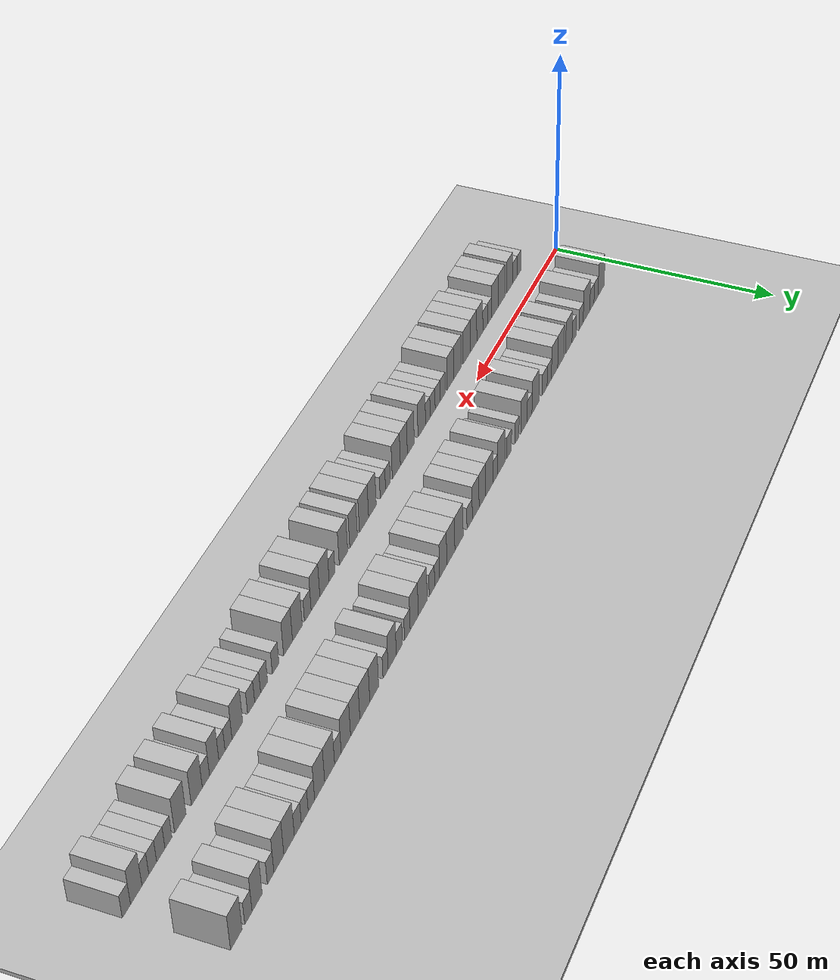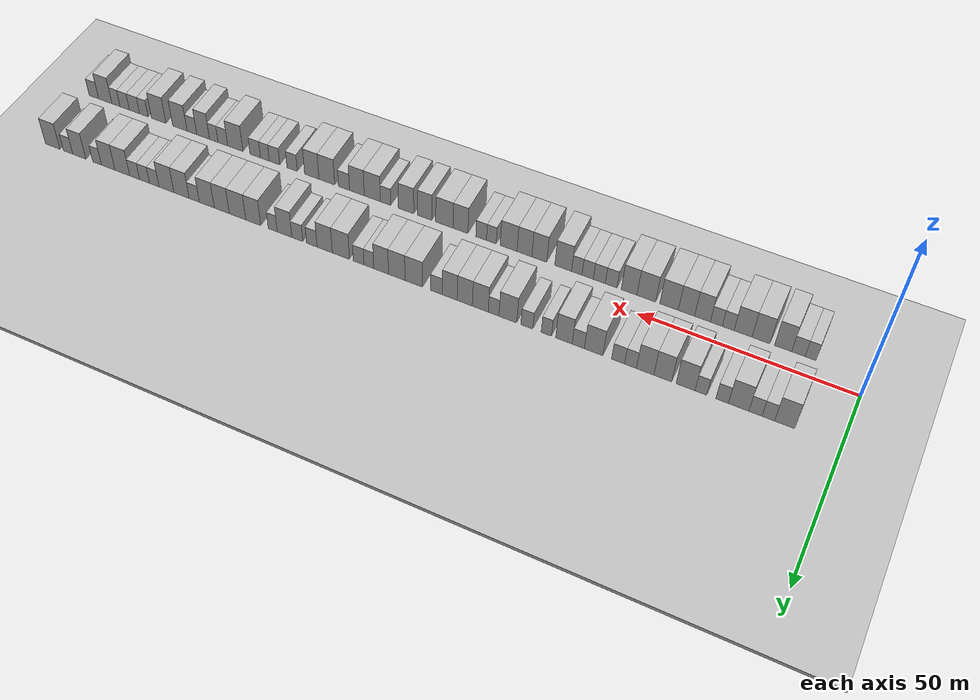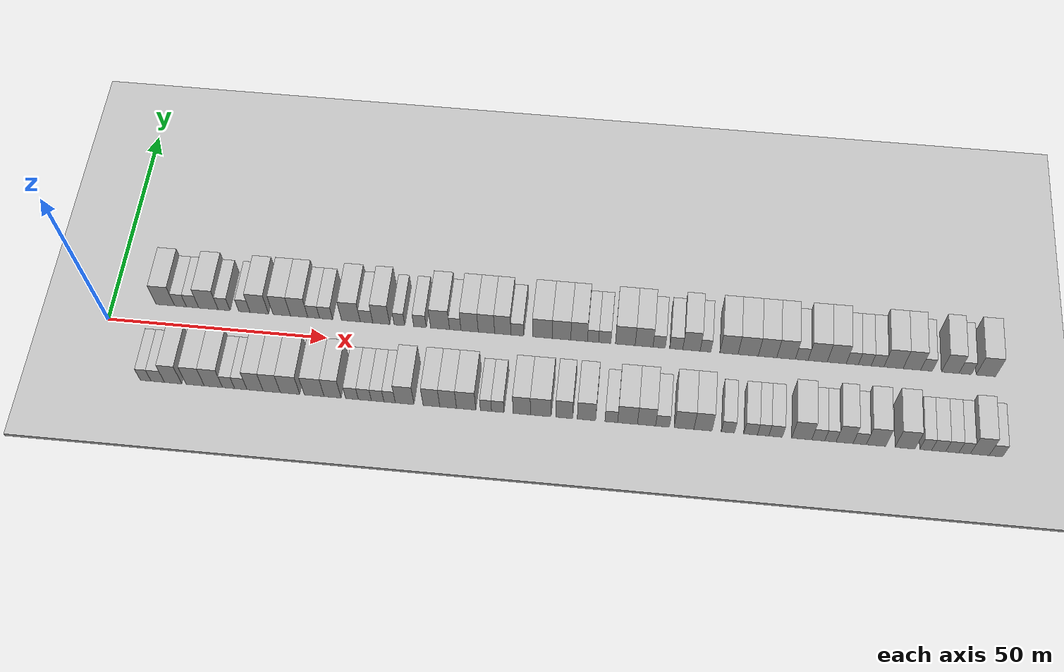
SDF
<?xml version="1.0" encoding="utf-8"?>

<sdf version="1.6">

   <world name="default">

      <gui fullscreen="0">

         <camera name="user_camera">

            <pose>-15 0 4.57585 0 0 0</pose>

            <view_controller>orbit</view_controller>

         </camera>

      </gui>

      <scene>

         <sky>

           <clouds>

             <speed>12</speed>

           </clouds>

         </sky>

         <ambient>0.4 0.4 0.4 1</ambient>

         <background>0.7 0.7 0.7 1</background>

         <shadows>1</shadows>

      </scene>

      <gravity>0 0 -9.8066</gravity>

      <magnetic_field>6e-06 2.3e-05 -4.2e-05</magnetic_field>

      <physics default="0" name="default_physics" type="ode">

         <ode>

            <solver>

               <type>quick</type>

               <iters>10</iters>

               <sor>1.0</sor>

               <use_dynamic_moi_rescaling>0</use_dynamic_moi_rescaling>

            </solver>

            <constraints>

               <cfm>0</cfm>

               <erp>0.2</erp>

               <contact_max_correcting_vel>100</contact_max_correcting_vel>

               <contact_surface_layer>0.001</contact_surface_layer>

            </constraints>

         </ode>

         <max_step_size>0.004</max_step_size>

         <real_time_factor>1</real_time_factor>

         <real_time_update_rate>250</real_time_update_rate>

      </physics>

      <light name="sun" type="directional">

         <cast_shadows>1</cast_shadows>

         <pose>0 0 10 0 0 0</pose>

         <diffuse>0.8 0.8 0.8 1</diffuse>

         <specular>0.2 0.2 0.2 1</specular>

         <attenuation>

            <range>1000</range>

            <constant>0.9</constant>

            <linear>0.01</linear>

            <quadratic>0.001</quadratic>

         </attenuation>

         <direction>-0.5 0.1 -0.9</direction>

      </light>

      <include>

         <name>ground_plane_1</name>

         <uri>model://HANNAS_ground_plane</uri>

         <pose>0 0 0  0 0 0</pose>

      </include>

      <include>

         <name>ground_plane_2</name>

         <uri>model://HANNAS_ground_plane</uri>

         <pose>100 0 0  0 0 0</pose>

      </include>

      <model name="building_1">

         <static>1</static>

         <pose frame="">12.1485 9.5000 0 0.000000 0.000000 1.570796</pose>

         <link name="link">

            <pose frame="">0 0 4.50 0 0 0</pose>

            <collision name="collision">

               <geometry>

                  <box>

                     <size>10.0000 4.2969 9.0000</size>

                  </box>

               </geometry>

               <max_contacts>10</max_contacts>

               <surface>

                  <contact>

                     <ode/>

                  </contact>

                  <bounce/>

                  <friction>

                     <torsional>

                        <ode/>

                     </torsional>

                     <ode/>

                  </friction>

               </surface>

            </collision>

            <visual name="visual">

               <cast_shadows>0</cast_shadows>

               <geometry>

                  <box>

                     <size>10.0000 4.2969 9.0000</size>

                  </box>

               </geometry>

               <material>

                  <script>

                     <uri>model://HANNAS_wall/materials/scripts</uri>

                     <uri>model://HANNAS_wall/materials/textures</uri>

                     <name>vrc/HANNAS_wall</name>

                  </script>

               </material>

            </visual>

            <self_collide>0</self_collide>

            <enable_wind>0</enable_wind>

            <kinematic>0</kinematic>

         </link>

      </model>

      <model name="building_2">

         <static>1</static>

         <pose frame="">15.6557 9.5000 0 0.000000 0.000000 1.570796</pose>

         <link name="link">

            <pose frame="">0 0 3.00 0 0 0</pose>

            <collision name="collision">

               <geometry>

                  <box>

                     <size>10.0000 2.7174 6.0000</size>

                  </box>

               </geometry>

               <max_contacts>10</max_contacts>

               <surface>

                  <contact>

                     <ode/>

                  </contact>

                  <bounce/>

                  <friction>

                     <torsional>

                        <ode/>

                     </torsional>

                     <ode/>

                  </friction>

               </surface>

            </collision>

            <visual name="visual">

               <cast_shadows>0</cast_shadows>

               <geometry>

                  <box>

                     <size>10.0000 2.7174 6.0000</size>

                  </box>

               </geometry>

               <material>

                  <script>

                     <uri>model://HANNAS_wall/materials/scripts</uri>

                     <uri>model://HANNAS_wall/materials/textures</uri>

                     <name>vrc/HANNAS_wall</name>

                  </script>

               </material>

            </visual>

            <self_collide>0</self_collide>

            <enable_wind>0</enable_wind>

            <kinematic>0</kinematic>

         </link>

      </model>

      <model name="building_3">

         <static>1</static>

         <pose frame="">18.4392 9.5000 0 0.000000 0.000000 1.570796</pose>

         <link name="link">

            <pose frame="">0 0 3.00 0 0 0</pose>

            <collision name="collision">

               <geometry>

                  <box>

                     <size>10.0000 2.8497 6.0000</size>

                  </box>

               </geometry>

               <max_contacts>10</max_contacts>

               <surface>

                  <contact>

                     <ode/>

                  </contact>

                  <bounce/>

                  <friction>

                     <torsional>

                        <ode/>

                     </torsional>

                     <ode/>

                  </friction>

               </surface>

            </collision>

            <visual name="visual">

               <cast_shadows>0</cast_shadows>

               <geometry>

                  <box>

                     <size>10.0000 2.8497 6.0000</size>

                  </box>

               </geometry>

               <material>

                  <script>

                     <uri>model://HANNAS_wall/materials/scripts</uri>

                     <uri>model://HANNAS_wall/materials/textures</uri>

                     <name>vrc/HANNAS_wall</name>

                  </script>

               </material>

            </visual>

            <self_collide>0</self_collide>

            <enable_wind>0</enable_wind>

            <kinematic>0</kinematic>

         </link>

      </model>

      <model name="building_4">

         <static>1</static>

         <pose frame="">22.0854 9.5000 0 0.000000 0.000000 1.570796</pose>

         <link name="link">

            <pose frame="">0 0 4.50 0 0 0</pose>

            <collision name="collision">

               <geometry>

                  <box>

                     <size>10.0000 4.4425 9.0000</size>

                  </box>

               </geometry>

               <max_contacts>10</max_contacts>

               <surface>

                  <contact>

                     <ode/>

                  </contact>

                  <bounce/>

                  <friction>

                     <torsional>

                        <ode/>

                     </torsional>

                     <ode/>

                  </friction>

               </surface>

            </collision>

            <visual name="visual">

               <cast_shadows>0</cast_shadows>

               <geometry>

                  <box>

                     <size>10.0000 4.4425 9.0000</size>

                  </box>

               </geometry>

               <material>

                  <script>

                     <uri>model://HANNAS_wall/materials/scripts</uri>

                     <uri>model://HANNAS_wall/materials/textures</uri>

                     <name>vrc/HANNAS_wall</name>

                  </script>

               </material>

            </visual>

            <self_collide>0</self_collide>

            <enable_wind>0</enable_wind>

            <kinematic>0</kinematic>

         </link>

      </model>

      <model name="building_5">

         <static>1</static>

         <pose frame="">25.6878 9.5000 0 0.000000 0.000000 1.570796</pose>

         <link name="link">

            <pose frame="">0 0 3.00 0 0 0</pose>

            <collision name="collision">

               <geometry>

                  <box>

                     <size>10.0000 2.7624 6.0000</size>

                  </box>

               </geometry>

               <max_contacts>10</max_contacts>

               <surface>

                  <contact>

                     <ode/>

                  </contact>

                  <bounce/>

                  <friction>

                     <torsional>

                        <ode/>

                     </torsional>

                     <ode/>

                  </friction>

               </surface>

            </collision>

            <visual name="visual">

               <cast_shadows>0</cast_shadows>

               <geometry>

                  <box>

                     <size>10.0000 2.7624 6.0000</size>

                  </box>

               </geometry>

               <material>

                  <script>

                     <uri>model://HANNAS_wall/materials/scripts</uri>

                     <uri>model://HANNAS_wall/materials/textures</uri>

                     <name>vrc/HANNAS_wall</name>

                  </script>

               </material>

            </visual>

            <self_collide>0</self_collide>

            <enable_wind>0</enable_wind>

            <kinematic>0</kinematic>

         </link>

      </model>

      <model name="building_6">

         <static>1</static>

         <pose frame="">30.3585 9.5000 0 0.000000 0.000000 1.570796</pose>

         <link name="link">

            <pose frame="">0 0 3.00 0 0 0</pose>

            <collision name="collision">

               <geometry>

                  <box>

                     <size>10.0000 2.5788 6.0000</size>

                  </box>

               </geometry>

               <max_contacts>10</max_contacts>

               <surface>

                  <contact>

                     <ode/>

                  </contact>

                  <bounce/>

                  <friction>

                     <torsional>

                        <ode/>

                     </torsional>

                     <ode/>

                  </friction>

               </surface>

            </collision>

            <visual name="visual">

               <cast_shadows>0</cast_shadows>

               <geometry>

                  <box>

                     <size>10.0000 2.5788 6.0000</size>

                  </box>

               </geometry>

               <material>

                  <script>

                     <uri>model://HANNAS_wall/materials/scripts</uri>

                     <uri>model://HANNAS_wall/materials/textures</uri>

                     <name>vrc/HANNAS_wall</name>

                  </script>

               </material>

            </visual>

            <self_collide>0</self_collide>

            <enable_wind>0</enable_wind>

            <kinematic>0</kinematic>

         </link>

      </model>

      <model name="building_7">

         <static>1</static>

         <pose frame="">33.7688 9.5000 0 0.000000 0.000000 1.570796</pose>

         <link name="link">

            <pose frame="">0 0 4.50 0 0 0</pose>

            <collision name="collision">

               <geometry>

                  <box>

                     <size>10.0000 4.2418 9.0000</size>

                  </box>

               </geometry>

               <max_contacts>10</max_contacts>

               <surface>

                  <contact>

                     <ode/>

                  </contact>

                  <bounce/>

                  <friction>

                     <torsional>

                        <ode/>

                     </torsional>

                     <ode/>

                  </friction>

               </surface>

            </collision>

            <visual name="visual">

               <cast_shadows>0</cast_shadows>

               <geometry>

                  <box>

                     <size>10.0000 4.2418 9.0000</size>

                  </box>

               </geometry>

               <material>

                  <script>

                     <uri>model://HANNAS_wall/materials/scripts</uri>

                     <uri>model://HANNAS_wall/materials/textures</uri>

                     <name>vrc/HANNAS_wall</name>

                  </script>

               </material>

            </visual>

            <self_collide>0</self_collide>

            <enable_wind>0</enable_wind>

            <kinematic>0</kinematic>

         </link>

      </model>

      <model name="building_8">

         <static>1</static>

         <pose frame="">38.8870 9.5000 0 0.000000 0.000000 1.570796</pose>

         <link name="link">

            <pose frame="">0 0 4.50 0 0 0</pose>

            <collision name="collision">

               <geometry>

                  <box>

                     <size>10.0000 3.9947 9.0000</size>

                  </box>

               </geometry>

               <max_contacts>10</max_contacts>

               <surface>

                  <contact>

                     <ode/>

                  </contact>

                  <bounce/>

                  <friction>

                     <torsional>

                        <ode/>

                     </torsional>

                     <ode/>

                  </friction>

               </surface>

            </collision>

            <visual name="visual">

               <cast_shadows>0</cast_shadows>

               <geometry>

                  <box>

                     <size>10.0000 3.9947 9.0000</size>

                  </box>

               </geometry>

               <material>

                  <script>

                     <uri>model://HANNAS_wall/materials/scripts</uri>

                     <uri>model://HANNAS_wall/materials/textures</uri>

                     <name>vrc/HANNAS_wall</name>

                  </script>

               </material>

            </visual>

            <self_collide>0</self_collide>

            <enable_wind>0</enable_wind>

            <kinematic>0</kinematic>

         </link>

      </model>

      <model name="building_9">

         <static>1</static>

         <pose frame="">42.8608 9.5000 0 0.000000 0.000000 1.570796</pose>

         <link name="link">

            <pose frame="">0 0 4.50 0 0 0</pose>

            <collision name="collision">

               <geometry>

                  <box>

                     <size>10.0000 3.9528 9.0000</size>

                  </box>

               </geometry>

               <max_contacts>10</max_contacts>

               <surface>

                  <contact>

                     <ode/>

                  </contact>

                  <bounce/>

                  <friction>

                     <torsional>

                        <ode/>

                     </torsional>

                     <ode/>

                  </friction>

               </surface>

            </collision>

            <visual name="visual">

               <cast_shadows>0</cast_shadows>

               <geometry>

                  <box>

                     <size>10.0000 3.9528 9.0000</size>

                  </box>

               </geometry>

               <material>

                  <script>

                     <uri>model://HANNAS_wall/materials/scripts</uri>

                     <uri>model://HANNAS_wall/materials/textures</uri>

                     <name>vrc/HANNAS_wall</name>

                  </script>

               </material>

            </visual>

            <self_collide>0</self_collide>

            <enable_wind>0</enable_wind>

            <kinematic>0</kinematic>

         </link>

      </model>

      <model name="building_10">

         <static>1</static>

         <pose frame="">46.1827 9.5000 0 0.000000 0.000000 1.570796</pose>

         <link name="link">

            <pose frame="">0 0 3.00 0 0 0</pose>

            <collision name="collision">

               <geometry>

                  <box>

                     <size>10.0000 2.6912 6.0000</size>

                  </box>

               </geometry>

               <max_contacts>10</max_contacts>

               <surface>

                  <contact>

                     <ode/>

                  </contact>

                  <bounce/>

                  <friction>

                     <torsional>

                        <ode/>

                     </torsional>

                     <ode/>

                  </friction>

               </surface>

            </collision>

            <visual name="visual">

               <cast_shadows>0</cast_shadows>

               <geometry>

                  <box>

                     <size>10.0000 2.6912 6.0000</size>

                  </box>

               </geometry>

               <material>

                  <script>

                     <uri>model://HANNAS_wall/materials/scripts</uri>

                     <uri>model://HANNAS_wall/materials/textures</uri>

                     <name>vrc/HANNAS_wall</name>

                  </script>

               </material>

            </visual>

            <self_collide>0</self_collide>

            <enable_wind>0</enable_wind>

            <kinematic>0</kinematic>

         </link>

      </model>

      <model name="building_11">

         <static>1</static>

         <pose frame="">49.0226 9.5000 0 0.000000 0.000000 1.570796</pose>

         <link name="link">

            <pose frame="">0 0 3.00 0 0 0</pose>

            <collision name="collision">

               <geometry>

                  <box>

                     <size>10.0000 2.9886 6.0000</size>

                  </box>

               </geometry>

               <max_contacts>10</max_contacts>

               <surface>

                  <contact>

                     <ode/>

                  </contact>

                  <bounce/>

                  <friction>

                     <torsional>

                        <ode/>

                     </torsional>

                     <ode/>

                  </friction>

               </surface>

            </collision>

            <visual name="visual">

               <cast_shadows>0</cast_shadows>

               <geometry>

                  <box>

                     <size>10.0000 2.9886 6.0000</size>

                  </box>

               </geometry>

               <material>

                  <script>

                     <uri>model://HANNAS_wall/materials/scripts</uri>

                     <uri>model://HANNAS_wall/materials/textures</uri>

                     <name>vrc/HANNAS_wall</name>

                  </script>

               </material>

            </visual>

            <self_collide>0</self_collide>

            <enable_wind>0</enable_wind>

            <kinematic>0</kinematic>

         </link>

      </model>

      <model name="building_12">

         <static>1</static>

         <pose frame="">54.6593 9.5000 0 0.000000 0.000000 1.570796</pose>

         <link name="link">

            <pose frame="">0 0 4.50 0 0 0</pose>

            <collision name="collision">

               <geometry>

                  <box>

                     <size>10.0000 4.2849 9.0000</size>

                  </box>

               </geometry>

               <max_contacts>10</max_contacts>

               <surface>

                  <contact>

                     <ode/>

                  </contact>

                  <bounce/>

                  <friction>

                     <torsional>

                        <ode/>

                     </torsional>

                     <ode/>

                  </friction>

               </surface>

            </collision>

            <visual name="visual">

               <cast_shadows>0</cast_shadows>

               <geometry>

                  <box>

                     <size>10.0000 4.2849 9.0000</size>

                  </box>

               </geometry>

               <material>

                  <script>

                     <uri>model://HANNAS_wall/materials/scripts</uri>

                     <uri>model://HANNAS_wall/materials/textures</uri>

                     <name>vrc/HANNAS_wall</name>

                  </script>

               </material>

            </visual>

            <self_collide>0</self_collide>

            <enable_wind>0</enable_wind>

            <kinematic>0</kinematic>

         </link>

      </model>

      <model name="building_13">

         <static>1</static>

         <pose frame="">58.2277 9.5000 0 0.000000 0.000000 1.570796</pose>

         <link name="link">

            <pose frame="">0 0 3.00 0 0 0</pose>

            <collision name="collision">

               <geometry>

                  <box>

                     <size>10.0000 2.8518 6.0000</size>

                  </box>

               </geometry>

               <max_contacts>10</max_contacts>

               <surface>

                  <contact>

                     <ode/>

                  </contact>

                  <bounce/>

                  <friction>

                     <torsional>

                        <ode/>

                     </torsional>

                     <ode/>

                  </friction>

               </surface>

            </collision>

            <visual name="visual">

               <cast_shadows>0</cast_shadows>

               <geometry>

                  <box>

                     <size>10.0000 2.8518 6.0000</size>

                  </box>

               </geometry>

               <material>

                  <script>

                     <uri>model://HANNAS_wall/materials/scripts</uri>

                     <uri>model://HANNAS_wall/materials/textures</uri>

                     <name>vrc/HANNAS_wall</name>

                  </script>

               </material>

            </visual>

            <self_collide>0</self_collide>

            <enable_wind>0</enable_wind>

            <kinematic>0</kinematic>

         </link>

      </model>

      <model name="building_14">

         <static>1</static>

         <pose frame="">61.5808 9.5000 0 0.000000 0.000000 1.570796</pose>

         <link name="link">

            <pose frame="">0 0 4.50 0 0 0</pose>

            <collision name="collision">

               <geometry>

                  <box>

                     <size>10.0000 3.8543 9.0000</size>

                  </box>

               </geometry>

               <max_contacts>10</max_contacts>

               <surface>

                  <contact>

                     <ode/>

                  </contact>

                  <bounce/>

                  <friction>

                     <torsional>

                        <ode/>

                     </torsional>

                     <ode/>

                  </friction>

               </surface>

            </collision>

            <visual name="visual">

               <cast_shadows>0</cast_shadows>

               <geometry>

                  <box>

                     <size>10.0000 3.8543 9.0000</size>

                  </box>

               </geometry>

               <material>

                  <script>

                     <uri>model://HANNAS_wall/materials/scripts</uri>

                     <uri>model://HANNAS_wall/materials/textures</uri>

                     <name>vrc/HANNAS_wall</name>

                  </script>

               </material>

            </visual>

            <self_collide>0</self_collide>

            <enable_wind>0</enable_wind>

            <kinematic>0</kinematic>

         </link>

      </model>

      <model name="building_15">

         <static>1</static>

         <pose frame="">65.7186 9.5000 0 0.000000 0.000000 1.570796</pose>

         <link name="link">

            <pose frame="">0 0 3.00 0 0 0</pose>

            <collision name="collision">

               <geometry>

                  <box>

                     <size>10.0000 2.4212 6.0000</size>

                  </box>

               </geometry>

               <max_contacts>10</max_contacts>

               <surface>

                  <contact>

                     <ode/>

                  </contact>

                  <bounce/>

                  <friction>

                     <torsional>

                        <ode/>

                     </torsional>

                     <ode/>

                  </friction>

               </surface>

            </collision>

            <visual name="visual">

               <cast_shadows>0</cast_shadows>

               <geometry>

                  <box>

                     <size>10.0000 2.4212 6.0000</size>

                  </box>

               </geometry>

               <material>

                  <script>

                     <uri>model://HANNAS_wall/materials/scripts</uri>

                     <uri>model://HANNAS_wall/materials/textures</uri>

                     <name>vrc/HANNAS_wall</name>

                  </script>

               </material>

            </visual>

            <self_collide>0</self_collide>

            <enable_wind>0</enable_wind>

            <kinematic>0</kinematic>

         </link>

      </model>

      <model name="building_16">

         <static>1</static>

         <pose frame="">70.3492 9.5000 0 0.000000 0.000000 1.570796</pose>

         <link name="link">

            <pose frame="">0 0 3.00 0 0 0</pose>

            <collision name="collision">

               <geometry>

                  <box>

                     <size>10.0000 2.8400 6.0000</size>

                  </box>

               </geometry>

               <max_contacts>10</max_contacts>

               <surface>

                  <contact>

                     <ode/>

                  </contact>

                  <bounce/>

                  <friction>

                     <torsional>

                        <ode/>

                     </torsional>

                     <ode/>

                  </friction>

               </surface>

            </collision>

            <visual name="visual">

               <cast_shadows>0</cast_shadows>

               <geometry>

                  <box>

                     <size>10.0000 2.8400 6.0000</size>

                  </box>

               </geometry>

               <material>

                  <script>

                     <uri>model://HANNAS_wall/materials/scripts</uri>

                     <uri>model://HANNAS_wall/materials/textures</uri>

                     <name>vrc/HANNAS_wall</name>

                  </script>

               </material>

            </visual>

            <self_collide>0</self_collide>

            <enable_wind>0</enable_wind>

            <kinematic>0</kinematic>

         </link>

      </model>

      <model name="building_17">

         <static>1</static>

         <pose frame="">74.9035 9.5000 0 0.000000 0.000000 1.570796</pose>

         <link name="link">

            <pose frame="">0 0 4.50 0 0 0</pose>

            <collision name="collision">

               <geometry>

                  <box>

                     <size>10.0000 4.2686 9.0000</size>

                  </box>

               </geometry>

               <max_contacts>10</max_contacts>

               <surface>

                  <contact>

                     <ode/>

                  </contact>

                  <bounce/>

                  <friction>

                     <torsional>

                        <ode/>

                     </torsional>

                     <ode/>

                  </friction>

               </surface>

            </collision>

            <visual name="visual">

               <cast_shadows>0</cast_shadows>

               <geometry>

                  <box>

                     <size>10.0000 4.2686 9.0000</size>

                  </box>

               </geometry>

               <material>

                  <script>

                     <uri>model://HANNAS_wall/materials/scripts</uri>

                     <uri>model://HANNAS_wall/materials/textures</uri>

                     <name>vrc/HANNAS_wall</name>

                  </script>

               </material>

            </visual>

            <self_collide>0</self_collide>

            <enable_wind>0</enable_wind>

            <kinematic>0</kinematic>

         </link>

      </model>

      <model name="building_18">

         <static>1</static>

         <pose frame="">78.3266 9.5000 0 0.000000 0.000000 1.570796</pose>

         <link name="link">

            <pose frame="">0 0 3.00 0 0 0</pose>

            <collision name="collision">

               <geometry>

                  <box>

                     <size>10.0000 2.5777 6.0000</size>

                  </box>

               </geometry>

               <max_contacts>10</max_contacts>

               <surface>

                  <contact>

                     <ode/>

                  </contact>

                  <bounce/>

                  <friction>

                     <torsional>

                        <ode/>

                     </torsional>

                     <ode/>

                  </friction>

               </surface>

            </collision>

            <visual name="visual">

               <cast_shadows>0</cast_shadows>

               <geometry>

                  <box>

                     <size>10.0000 2.5777 6.0000</size>

                  </box>

               </geometry>

               <material>

                  <script>

                     <uri>model://HANNAS_wall/materials/scripts</uri>

                     <uri>model://HANNAS_wall/materials/textures</uri>

                     <name>vrc/HANNAS_wall</name>

                  </script>

               </material>

            </visual>

            <self_collide>0</self_collide>

            <enable_wind>0</enable_wind>

            <kinematic>0</kinematic>

         </link>

      </model>

      <model name="building_19">

         <static>1</static>

         <pose frame="">81.5625 9.5000 0 0.000000 0.000000 1.570796</pose>

         <link name="link">

            <pose frame="">0 0 4.50 0 0 0</pose>

            <collision name="collision">

               <geometry>

                  <box>

                     <size>10.0000 3.8939 9.0000</size>

                  </box>

               </geometry>

               <max_contacts>10</max_contacts>

               <surface>

                  <contact>

                     <ode/>

                  </contact>

                  <bounce/>

                  <friction>

                     <torsional>

                        <ode/>

                     </torsional>

                     <ode/>

                  </friction>

               </surface>

            </collision>

            <visual name="visual">

               <cast_shadows>0</cast_shadows>

               <geometry>

                  <box>

                     <size>10.0000 3.8939 9.0000</size>

                  </box>

               </geometry>

               <material>

                  <script>

                     <uri>model://HANNAS_wall/materials/scripts</uri>

                     <uri>model://HANNAS_wall/materials/textures</uri>

                     <name>vrc/HANNAS_wall</name>

                  </script>

               </material>

            </visual>

            <self_collide>0</self_collide>

            <enable_wind>0</enable_wind>

            <kinematic>0</kinematic>

         </link>

      </model>

      <model name="building_20">

         <static>1</static>

         <pose frame="">85.3593 9.5000 0 0.000000 0.000000 1.570796</pose>

         <link name="link">

            <pose frame="">0 0 4.50 0 0 0</pose>

            <collision name="collision">

               <geometry>

                  <box>

                     <size>10.0000 3.6998 9.0000</size>

                  </box>

               </geometry>

               <max_contacts>10</max_contacts>

               <surface>

                  <contact>

                     <ode/>

                  </contact>

                  <bounce/>

                  <friction>

                     <torsional>

                        <ode/>

                     </torsional>

                     <ode/>

                  </friction>

               </surface>

            </collision>

            <visual name="visual">

               <cast_shadows>0</cast_shadows>

               <geometry>

                  <box>

                     <size>10.0000 3.6998 9.0000</size>

                  </box>

               </geometry>

               <material>

                  <script>

                     <uri>model://HANNAS_wall/materials/scripts</uri>

                     <uri>model://HANNAS_wall/materials/textures</uri>

                     <name>vrc/HANNAS_wall</name>

                  </script>

               </material>

            </visual>

            <self_collide>0</self_collide>

            <enable_wind>0</enable_wind>

            <kinematic>0</kinematic>

         </link>

      </model>

      <model name="building_21">

         <static>1</static>

         <pose frame="">89.0442 9.5000 0 0.000000 0.000000 1.570796</pose>

         <link name="link">

            <pose frame="">0 0 4.50 0 0 0</pose>

            <collision name="collision">

               <geometry>

                  <box>

                     <size>10.0000 3.6701 9.0000</size>

                  </box>

               </geometry>

               <max_contacts>10</max_contacts>

               <surface>

                  <contact>

                     <ode/>

                  </contact>

                  <bounce/>

                  <friction>

                     <torsional>

                        <ode/>

                     </torsional>

                     <ode/>

                  </friction>

               </surface>

            </collision>

            <visual name="visual">

               <cast_shadows>0</cast_shadows>

               <geometry>

                  <box>

                     <size>10.0000 3.6701 9.0000</size>

                  </box>

               </geometry>

               <material>

                  <script>

                     <uri>model://HANNAS_wall/materials/scripts</uri>

                     <uri>model://HANNAS_wall/materials/textures</uri>

                     <name>vrc/HANNAS_wall</name>

                  </script>

               </material>

            </visual>

            <self_collide>0</self_collide>

            <enable_wind>0</enable_wind>

            <kinematic>0</kinematic>

         </link>

      </model>

      <model name="building_22">

         <static>1</static>

         <pose frame="">92.3200 9.5000 0 0.000000 0.000000 1.570796</pose>

         <link name="link">

            <pose frame="">0 0 3.00 0 0 0</pose>

            <collision name="collision">

               <geometry>

                  <box>

                     <size>10.0000 2.8814 6.0000</size>

                  </box>

               </geometry>

               <max_contacts>10</max_contacts>

               <surface>

                  <contact>

                     <ode/>

                  </contact>

                  <bounce/>

                  <friction>

                     <torsional>

                        <ode/>

                     </torsional>

                     <ode/>

                  </friction>

               </surface>

            </collision>

            <visual name="visual">

               <cast_shadows>0</cast_shadows>

               <geometry>

                  <box>

                     <size>10.0000 2.8814 6.0000</size>

                  </box>

               </geometry>

               <material>

                  <script>

                     <uri>model://HANNAS_wall/materials/scripts</uri>

                     <uri>model://HANNAS_wall/materials/textures</uri>

                     <name>vrc/HANNAS_wall</name>

                  </script>

               </material>

            </visual>

            <self_collide>0</self_collide>

            <enable_wind>0</enable_wind>

            <kinematic>0</kinematic>

         </link>

      </model>

      <model name="building_23">

         <static>1</static>

         <pose frame="">97.9645 9.5000 0 0.000000 0.000000 1.570796</pose>

         <link name="link">

            <pose frame="">0 0 4.50 0 0 0</pose>

            <collision name="collision">

               <geometry>

                  <box>

                     <size>10.0000 4.4076 9.0000</size>

                  </box>

               </geometry>

               <max_contacts>10</max_contacts>

               <surface>

                  <contact>

                     <ode/>

                  </contact>

                  <bounce/>

                  <friction>

                     <torsional>

                        <ode/>

                     </torsional>

                     <ode/>

                  </friction>

               </surface>

            </collision>

            <visual name="visual">

               <cast_shadows>0</cast_shadows>

               <geometry>

                  <box>

                     <size>10.0000 4.4076 9.0000</size>

                  </box>

               </geometry>

               <material>

                  <script>

                     <uri>model://HANNAS_wall/materials/scripts</uri>

                     <uri>model://HANNAS_wall/materials/textures</uri>

                     <name>vrc/HANNAS_wall</name>

                  </script>

               </material>

            </visual>

            <self_collide>0</self_collide>

            <enable_wind>0</enable_wind>

            <kinematic>0</kinematic>

         </link>

      </model>

      <model name="building_24">

         <static>1</static>

         <pose frame="">102.2498 9.5000 0 0.000000 0.000000 1.570796</pose>

         <link name="link">

            <pose frame="">0 0 4.50 0 0 0</pose>

            <collision name="collision">

               <geometry>

                  <box>

                     <size>10.0000 4.1629 9.0000</size>

                  </box>

               </geometry>

               <max_contacts>10</max_contacts>

               <surface>

                  <contact>

                     <ode/>

                  </contact>

                  <bounce/>

                  <friction>

                     <torsional>

                        <ode/>

                     </torsional>

                     <ode/>

                  </friction>

               </surface>

            </collision>

            <visual name="visual">

               <cast_shadows>0</cast_shadows>

               <geometry>

                  <box>

                     <size>10.0000 4.1629 9.0000</size>

                  </box>

               </geometry>

               <material>

                  <script>

                     <uri>model://HANNAS_wall/materials/scripts</uri>

                     <uri>model://HANNAS_wall/materials/textures</uri>

                     <name>vrc/HANNAS_wall</name>

                  </script>

               </material>

            </visual>

            <self_collide>0</self_collide>

            <enable_wind>0</enable_wind>

            <kinematic>0</kinematic>

         </link>

      </model>

      <model name="building_25">

         <static>1</static>

         <pose frame="">106.1985 9.5000 0 0.000000 0.000000 1.570796</pose>

         <link name="link">

            <pose frame="">0 0 4.50 0 0 0</pose>

            <collision name="collision">

               <geometry>

                  <box>

                     <size>10.0000 3.7347 9.0000</size>

                  </box>

               </geometry>

               <max_contacts>10</max_contacts>

               <surface>

                  <contact>

                     <ode/>

                  </contact>

                  <bounce/>

                  <friction>

                     <torsional>

                        <ode/>

                     </torsional>

                     <ode/>

                  </friction>

               </surface>

            </collision>

            <visual name="visual">

               <cast_shadows>0</cast_shadows>

               <geometry>

                  <box>

                     <size>10.0000 3.7347 9.0000</size>

                  </box>

               </geometry>

               <material>

                  <script>

                     <uri>model://HANNAS_wall/materials/scripts</uri>

                     <uri>model://HANNAS_wall/materials/textures</uri>

                     <name>vrc/HANNAS_wall</name>

                  </script>

               </material>

            </visual>

            <self_collide>0</self_collide>

            <enable_wind>0</enable_wind>

            <kinematic>0</kinematic>

         </link>

      </model>

      <model name="building_26">

         <static>1</static>

         <pose frame="">109.3079 9.5000 0 0.000000 0.000000 1.570796</pose>

         <link name="link">

            <pose frame="">0 0 3.00 0 0 0</pose>

            <collision name="collision">

               <geometry>

                  <box>

                     <size>10.0000 2.4841 6.0000</size>

                  </box>

               </geometry>

               <max_contacts>10</max_contacts>

               <surface>

                  <contact>

                     <ode/>

                  </contact>

                  <bounce/>

                  <friction>

                     <torsional>

                        <ode/>

                     </torsional>

                     <ode/>

                  </friction>

               </surface>

            </collision>

            <visual name="visual">

               <cast_shadows>0</cast_shadows>

               <geometry>

                  <box>

                     <size>10.0000 2.4841 6.0000</size>

                  </box>

               </geometry>

               <material>

                  <script>

                     <uri>model://HANNAS_wall/materials/scripts</uri>

                     <uri>model://HANNAS_wall/materials/textures</uri>

                     <name>vrc/HANNAS_wall</name>

                  </script>

               </material>

            </visual>

            <self_collide>0</self_collide>

            <enable_wind>0</enable_wind>

            <kinematic>0</kinematic>

         </link>

      </model>

      <model name="building_27">

         <static>1</static>

         <pose frame="">111.9256 9.5000 0 0.000000 0.000000 1.570796</pose>

         <link name="link">

            <pose frame="">0 0 3.00 0 0 0</pose>

            <collision name="collision">

               <geometry>

                  <box>

                     <size>10.0000 2.7511 6.0000</size>

                  </box>

               </geometry>

               <max_contacts>10</max_contacts>

               <surface>

                  <contact>

                     <ode/>

                  </contact>

                  <bounce/>

                  <friction>

                     <torsional>

                        <ode/>

                     </torsional>

                     <ode/>

                  </friction>

               </surface>

            </collision>

            <visual name="visual">

               <cast_shadows>0</cast_shadows>

               <geometry>

                  <box>

                     <size>10.0000 2.7511 6.0000</size>

                  </box>

               </geometry>

               <material>

                  <script>

                     <uri>model://HANNAS_wall/materials/scripts</uri>

                     <uri>model://HANNAS_wall/materials/textures</uri>

                     <name>vrc/HANNAS_wall</name>

                  </script>

               </material>

            </visual>

            <self_collide>0</self_collide>

            <enable_wind>0</enable_wind>

            <kinematic>0</kinematic>

         </link>

      </model>

      <model name="building_28">

         <static>1</static>

         <pose frame="">116.5041 9.5000 0 0.000000 0.000000 1.570796</pose>

         <link name="link">

            <pose frame="">0 0 4.50 0 0 0</pose>

            <collision name="collision">

               <geometry>

                  <box>

                     <size>10.0000 4.4059 9.0000</size>

                  </box>

               </geometry>

               <max_contacts>10</max_contacts>

               <surface>

                  <contact>

                     <ode/>

                  </contact>

                  <bounce/>

                  <friction>

                     <torsional>

                        <ode/>

                     </torsional>

                     <ode/>

                  </friction>

               </surface>

            </collision>

            <visual name="visual">

               <cast_shadows>0</cast_shadows>

               <geometry>

                  <box>

                     <size>10.0000 4.4059 9.0000</size>

                  </box>

               </geometry>

               <material>

                  <script>

                     <uri>model://HANNAS_wall/materials/scripts</uri>

                     <uri>model://HANNAS_wall/materials/textures</uri>

                     <name>vrc/HANNAS_wall</name>

                  </script>

               </material>

            </visual>

            <self_collide>0</self_collide>

            <enable_wind>0</enable_wind>

            <kinematic>0</kinematic>

         </link>

      </model>

      <model name="building_29">

         <static>1</static>

         <pose frame="">120.6980 9.5000 0 0.000000 0.000000 1.570796</pose>

         <link name="link">

            <pose frame="">0 0 4.50 0 0 0</pose>

            <collision name="collision">

               <geometry>

                  <box>

                     <size>10.0000 3.9819 9.0000</size>

                  </box>

               </geometry>

               <max_contacts>10</max_contacts>

               <surface>

                  <contact>

                     <ode/>

                  </contact>

                  <bounce/>

                  <friction>

                     <torsional>

                        <ode/>

                     </torsional>

                     <ode/>

                  </friction>

               </surface>

            </collision>

            <visual name="visual">

               <cast_shadows>0</cast_shadows>

               <geometry>

                  <box>

                     <size>10.0000 3.9819 9.0000</size>

                  </box>

               </geometry>

               <material>

                  <script>

                     <uri>model://HANNAS_wall/materials/scripts</uri>

                     <uri>model://HANNAS_wall/materials/textures</uri>

                     <name>vrc/HANNAS_wall</name>

                  </script>

               </material>

            </visual>

            <self_collide>0</self_collide>

            <enable_wind>0</enable_wind>

            <kinematic>0</kinematic>

         </link>

      </model>

      <model name="building_30">

         <static>1</static>

         <pose frame="">124.0550 9.5000 0 0.000000 0.000000 1.570796</pose>

         <link name="link">

            <pose frame="">0 0 3.00 0 0 0</pose>

            <collision name="collision">

               <geometry>

                  <box>

                     <size>10.0000 2.7321 6.0000</size>

                  </box>

               </geometry>

               <max_contacts>10</max_contacts>

               <surface>

                  <contact>

                     <ode/>

                  </contact>

                  <bounce/>

                  <friction>

                     <torsional>

                        <ode/>

                     </torsional>

                     <ode/>

                  </friction>

               </surface>

            </collision>

            <visual name="visual">

               <cast_shadows>0</cast_shadows>

               <geometry>

                  <box>

                     <size>10.0000 2.7321 6.0000</size>

                  </box>

               </geometry>

               <material>

                  <script>

                     <uri>model://HANNAS_wall/materials/scripts</uri>

                     <uri>model://HANNAS_wall/materials/textures</uri>

                     <name>vrc/HANNAS_wall</name>

                  </script>

               </material>

            </visual>

            <self_collide>0</self_collide>

            <enable_wind>0</enable_wind>

            <kinematic>0</kinematic>

         </link>

      </model>

      <model name="building_31">

         <static>1</static>

         <pose frame="">127.8706 9.5000 0 0.000000 0.000000 1.570796</pose>

         <link name="link">

            <pose frame="">0 0 3.00 0 0 0</pose>

            <collision name="collision">

               <geometry>

                  <box>

                     <size>10.0000 2.8991 6.0000</size>

                  </box>

               </geometry>

               <max_contacts>10</max_contacts>

               <surface>

                  <contact>

                     <ode/>

                  </contact>

                  <bounce/>

                  <friction>

                     <torsional>

                        <ode/>

                     </torsional>

                     <ode/>

                  </friction>

               </surface>

            </collision>

            <visual name="visual">

               <cast_shadows>0</cast_shadows>

               <geometry>

                  <box>

                     <size>10.0000 2.8991 6.0000</size>

                  </box>

               </geometry>

               <material>

                  <script>

                     <uri>model://HANNAS_wall/materials/scripts</uri>

                     <uri>model://HANNAS_wall/materials/textures</uri>

                     <name>vrc/HANNAS_wall</name>

                  </script>

               </material>

            </visual>

            <self_collide>0</self_collide>

            <enable_wind>0</enable_wind>

            <kinematic>0</kinematic>

         </link>

      </model>

      <model name="building_32">

         <static>1</static>

         <pose frame="">131.2488 9.5000 0 0.000000 0.000000 1.570796</pose>

         <link name="link">

            <pose frame="">0 0 4.50 0 0 0</pose>

            <collision name="collision">

               <geometry>

                  <box>

                     <size>10.0000 3.8573 9.0000</size>

                  </box>

               </geometry>

               <max_contacts>10</max_contacts>

               <surface>

                  <contact>

                     <ode/>

                  </contact>

                  <bounce/>

                  <friction>

                     <torsional>

                        <ode/>

                     </torsional>

                     <ode/>

                  </friction>

               </surface>

            </collision>

            <visual name="visual">

               <cast_shadows>0</cast_shadows>

               <geometry>

                  <box>

                     <size>10.0000 3.8573 9.0000</size>

                  </box>

               </geometry>

               <material>

                  <script>

                     <uri>model://HANNAS_wall/materials/scripts</uri>

                     <uri>model://HANNAS_wall/materials/textures</uri>

                     <name>vrc/HANNAS_wall</name>

                  </script>

               </material>

            </visual>

            <self_collide>0</self_collide>

            <enable_wind>0</enable_wind>

            <kinematic>0</kinematic>

         </link>

      </model>

      <model name="building_33">

         <static>1</static>

         <pose frame="">134.3775 9.5000 0 0.000000 0.000000 1.570796</pose>

         <link name="link">

            <pose frame="">0 0 3.00 0 0 0</pose>

            <collision name="collision">

               <geometry>

                  <box>

                     <size>10.0000 2.4002 6.0000</size>

                  </box>

               </geometry>

               <max_contacts>10</max_contacts>

               <surface>

                  <contact>

                     <ode/>

                  </contact>

                  <bounce/>

                  <friction>

                     <torsional>

                        <ode/>

                     </torsional>

                     <ode/>

                  </friction>

               </surface>

            </collision>

            <visual name="visual">

               <cast_shadows>0</cast_shadows>

               <geometry>

                  <box>

                     <size>10.0000 2.4002 6.0000</size>

                  </box>

               </geometry>

               <material>

                  <script>

                     <uri>model://HANNAS_wall/materials/scripts</uri>

                     <uri>model://HANNAS_wall/materials/textures</uri>

                     <name>vrc/HANNAS_wall</name>

                  </script>

               </material>

            </visual>

            <self_collide>0</self_collide>

            <enable_wind>0</enable_wind>

            <kinematic>0</kinematic>

         </link>

      </model>

      <model name="building_34">

         <static>1</static>

         <pose frame="">139.5908 9.5000 0 0.000000 0.000000 1.570796</pose>

         <link name="link">

            <pose frame="">0 0 4.50 0 0 0</pose>

            <collision name="collision">

               <geometry>

                  <box>

                     <size>10.0000 4.0264 9.0000</size>

                  </box>

               </geometry>

               <max_contacts>10</max_contacts>

               <surface>

                  <contact>

                     <ode/>

                  </contact>

                  <bounce/>

                  <friction>

                     <torsional>

                        <ode/>

                     </torsional>

                     <ode/>

                  </friction>

               </surface>

            </collision>

            <visual name="visual">

               <cast_shadows>0</cast_shadows>

               <geometry>

                  <box>

                     <size>10.0000 4.0264 9.0000</size>

                  </box>

               </geometry>

               <material>

                  <script>

                     <uri>model://HANNAS_wall/materials/scripts</uri>

                     <uri>model://HANNAS_wall/materials/textures</uri>

                     <name>vrc/HANNAS_wall</name>

                  </script>

               </material>

            </visual>

            <self_collide>0</self_collide>

            <enable_wind>0</enable_wind>

            <kinematic>0</kinematic>

         </link>

      </model>

      <model name="building_35">

         <static>1</static>

         <pose frame="">143.8461 9.5000 0 0.000000 0.000000 1.570796</pose>

         <link name="link">

            <pose frame="">0 0 4.50 0 0 0</pose>

            <collision name="collision">

               <geometry>

                  <box>

                     <size>10.0000 4.4843 9.0000</size>

                  </box>

               </geometry>

               <max_contacts>10</max_contacts>

               <surface>

                  <contact>

                     <ode/>

                  </contact>

                  <bounce/>

                  <friction>

                     <torsional>

                        <ode/>

                     </torsional>

                     <ode/>

                  </friction>

               </surface>

            </collision>

            <visual name="visual">

               <cast_shadows>0</cast_shadows>

               <geometry>

                  <box>

                     <size>10.0000 4.4843 9.0000</size>

                  </box>

               </geometry>

               <material>

                  <script>

                     <uri>model://HANNAS_wall/materials/scripts</uri>

                     <uri>model://HANNAS_wall/materials/textures</uri>

                     <name>vrc/HANNAS_wall</name>

                  </script>

               </material>

            </visual>

            <self_collide>0</self_collide>

            <enable_wind>0</enable_wind>

            <kinematic>0</kinematic>

         </link>

      </model>

      <model name="building_36">

         <static>1</static>

         <pose frame="">148.1364 9.5000 0 0.000000 0.000000 1.570796</pose>

         <link name="link">

            <pose frame="">0 0 4.50 0 0 0</pose>

            <collision name="collision">

               <geometry>

                  <box>

                     <size>10.0000 4.0963 9.0000</size>

                  </box>

               </geometry>

               <max_contacts>10</max_contacts>

               <surface>

                  <contact>

                     <ode/>

                  </contact>

                  <bounce/>

                  <friction>

                     <torsional>

                        <ode/>

                     </torsional>

                     <ode/>

                  </friction>

               </surface>

            </collision>

            <visual name="visual">

               <cast_shadows>0</cast_shadows>

               <geometry>

                  <box>

                     <size>10.0000 4.0963 9.0000</size>

                  </box>

               </geometry>

               <material>

                  <script>

                     <uri>model://HANNAS_wall/materials/scripts</uri>

                     <uri>model://HANNAS_wall/materials/textures</uri>

                     <name>vrc/HANNAS_wall</name>

                  </script>

               </material>

            </visual>

            <self_collide>0</self_collide>

            <enable_wind>0</enable_wind>

            <kinematic>0</kinematic>

         </link>

      </model>

      <model name="building_37">

         <static>1</static>

         <pose frame="">152.2418 9.5000 0 0.000000 0.000000 1.570796</pose>

         <link name="link">

            <pose frame="">0 0 4.50 0 0 0</pose>

            <collision name="collision">

               <geometry>

                  <box>

                     <size>10.0000 4.1145 9.0000</size>

                  </box>

               </geometry>

               <max_contacts>10</max_contacts>

               <surface>

                  <contact>

                     <ode/>

                  </contact>

                  <bounce/>

                  <friction>

                     <torsional>

                        <ode/>

                     </torsional>

                     <ode/>

                  </friction>

               </surface>

            </collision>

            <visual name="visual">

               <cast_shadows>0</cast_shadows>

               <geometry>

                  <box>

                     <size>10.0000 4.1145 9.0000</size>

                  </box>

               </geometry>

               <material>

                  <script>

                     <uri>model://HANNAS_wall/materials/scripts</uri>

                     <uri>model://HANNAS_wall/materials/textures</uri>

                     <name>vrc/HANNAS_wall</name>

                  </script>

               </material>

            </visual>

            <self_collide>0</self_collide>

            <enable_wind>0</enable_wind>

            <kinematic>0</kinematic>

         </link>

      </model>

      <model name="building_38">

         <static>1</static>

         <pose frame="">155.6980 9.5000 0 0.000000 0.000000 1.570796</pose>

         <link name="link">

            <pose frame="">0 0 3.00 0 0 0</pose>

            <collision name="collision">

               <geometry>

                  <box>

                     <size>10.0000 2.7979 6.0000</size>

                  </box>

               </geometry>

               <max_contacts>10</max_contacts>

               <surface>

                  <contact>

                     <ode/>

                  </contact>

                  <bounce/>

                  <friction>

                     <torsional>

                        <ode/>

                     </torsional>

                     <ode/>

                  </friction>

               </surface>

            </collision>

            <visual name="visual">

               <cast_shadows>0</cast_shadows>

               <geometry>

                  <box>

                     <size>10.0000 2.7979 6.0000</size>

                  </box>

               </geometry>

               <material>

                  <script>

                     <uri>model://HANNAS_wall/materials/scripts</uri>

                     <uri>model://HANNAS_wall/materials/textures</uri>

                     <name>vrc/HANNAS_wall</name>

                  </script>

               </material>

            </visual>

            <self_collide>0</self_collide>

            <enable_wind>0</enable_wind>

            <kinematic>0</kinematic>

         </link>

      </model>

      <model name="building_39">

         <static>1</static>

         <pose frame="">159.2119 9.5000 0 0.000000 0.000000 1.570796</pose>

         <link name="link">

            <pose frame="">0 0 4.50 0 0 0</pose>

            <collision name="collision">

               <geometry>

                  <box>

                     <size>10.0000 4.2299 9.0000</size>

                  </box>

               </geometry>

               <max_contacts>10</max_contacts>

               <surface>

                  <contact>

                     <ode/>

                  </contact>

                  <bounce/>

                  <friction>

                     <torsional>

                        <ode/>

                     </torsional>

                     <ode/>

                  </friction>

               </surface>

            </collision>

            <visual name="visual">

               <cast_shadows>0</cast_shadows>

               <geometry>

                  <box>

                     <size>10.0000 4.2299 9.0000</size>

                  </box>

               </geometry>

               <material>

                  <script>

                     <uri>model://HANNAS_wall/materials/scripts</uri>

                     <uri>model://HANNAS_wall/materials/textures</uri>

                     <name>vrc/HANNAS_wall</name>

                  </script>

               </material>

            </visual>

            <self_collide>0</self_collide>

            <enable_wind>0</enable_wind>

            <kinematic>0</kinematic>

         </link>

      </model>

      <model name="building_40">

         <static>1</static>

         <pose frame="">163.4170 9.5000 0 0.000000 0.000000 1.570796</pose>

         <link name="link">

            <pose frame="">0 0 4.50 0 0 0</pose>

            <collision name="collision">

               <geometry>

                  <box>

                     <size>10.0000 4.1805 9.0000</size>

                  </box>

               </geometry>

               <max_contacts>10</max_contacts>

               <surface>

                  <contact>

                     <ode/>

                  </contact>

                  <bounce/>

                  <friction>

                     <torsional>

                        <ode/>

                     </torsional>

                     <ode/>

                  </friction>

               </surface>

            </collision>

            <visual name="visual">

               <cast_shadows>0</cast_shadows>

               <geometry>

                  <box>

                     <size>10.0000 4.1805 9.0000</size>

                  </box>

               </geometry>

               <material>

                  <script>

                     <uri>model://HANNAS_wall/materials/scripts</uri>

                     <uri>model://HANNAS_wall/materials/textures</uri>

                     <name>vrc/HANNAS_wall</name>

                  </script>

               </material>

            </visual>

            <self_collide>0</self_collide>

            <enable_wind>0</enable_wind>

            <kinematic>0</kinematic>

         </link>

      </model>

      <model name="building_41">

         <static>1</static>

         <pose frame="">166.8425 9.5000 0 0.000000 0.000000 1.570796</pose>

         <link name="link">

            <pose frame="">0 0 3.00 0 0 0</pose>

            <collision name="collision">

               <geometry>

                  <box>

                     <size>10.0000 2.6705 6.0000</size>

                  </box>

               </geometry>

               <max_contacts>10</max_contacts>

               <surface>

                  <contact>

                     <ode/>

                  </contact>

                  <bounce/>

                  <friction>

                     <torsional>

                        <ode/>

                     </torsional>

                     <ode/>

                  </friction>

               </surface>

            </collision>

            <visual name="visual">

               <cast_shadows>0</cast_shadows>

               <geometry>

                  <box>

                     <size>10.0000 2.6705 6.0000</size>

                  </box>

               </geometry>

               <material>

                  <script>

                     <uri>model://HANNAS_wall/materials/scripts</uri>

                     <uri>model://HANNAS_wall/materials/textures</uri>

                     <name>vrc/HANNAS_wall</name>

                  </script>

               </material>

            </visual>

            <self_collide>0</self_collide>

            <enable_wind>0</enable_wind>

            <kinematic>0</kinematic>

         </link>

      </model>

      <model name="building_42">

         <static>1</static>

         <pose frame="">169.5877 9.5000 0 0.000000 0.000000 1.570796</pose>

         <link name="link">

            <pose frame="">0 0 3.00 0 0 0</pose>

            <collision name="collision">

               <geometry>

                  <box>

                     <size>10.0000 2.8198 6.0000</size>

                  </box>

               </geometry>

               <max_contacts>10</max_contacts>

               <surface>

                  <contact>

                     <ode/>

                  </contact>

                  <bounce/>

                  <friction>

                     <torsional>

                        <ode/>

                     </torsional>

                     <ode/>

                  </friction>

               </surface>

            </collision>

            <visual name="visual">

               <cast_shadows>0</cast_shadows>

               <geometry>

                  <box>

                     <size>10.0000 2.8198 6.0000</size>

                  </box>

               </geometry>

               <material>

                  <script>

                     <uri>model://HANNAS_wall/materials/scripts</uri>

                     <uri>model://HANNAS_wall/materials/textures</uri>

                     <name>vrc/HANNAS_wall</name>

                  </script>

               </material>

            </visual>

            <self_collide>0</self_collide>

            <enable_wind>0</enable_wind>

            <kinematic>0</kinematic>

         </link>

      </model>

      <model name="building_43">

         <static>1</static>

         <pose frame="">172.3979 9.5000 0 0.000000 0.000000 1.570796</pose>

         <link name="link">

            <pose frame="">0 0 3.00 0 0 0</pose>

            <collision name="collision">

               <geometry>

                  <box>

                     <size>10.0000 2.8007 6.0000</size>

                  </box>

               </geometry>

               <max_contacts>10</max_contacts>

               <surface>

                  <contact>

                     <ode/>

                  </contact>

                  <bounce/>

                  <friction>

                     <torsional>

                        <ode/>

                     </torsional>

                     <ode/>

                  </friction>

               </surface>

            </collision>

            <visual name="visual">

               <cast_shadows>0</cast_shadows>

               <geometry>

                  <box>

                     <size>10.0000 2.8007 6.0000</size>

                  </box>

               </geometry>

               <material>

                  <script>

                     <uri>model://HANNAS_wall/materials/scripts</uri>

                     <uri>model://HANNAS_wall/materials/textures</uri>

                     <name>vrc/HANNAS_wall</name>

                  </script>

               </material>

            </visual>

            <self_collide>0</self_collide>

            <enable_wind>0</enable_wind>

            <kinematic>0</kinematic>

         </link>

      </model>

      <model name="building_44">

         <static>1</static>

         <pose frame="">175.9020 9.5000 0 0.000000 0.000000 1.570796</pose>

         <link name="link">

            <pose frame="">0 0 4.50 0 0 0</pose>

            <collision name="collision">

               <geometry>

                  <box>

                     <size>10.0000 4.2075 9.0000</size>

                  </box>

               </geometry>

               <max_contacts>10</max_contacts>

               <surface>

                  <contact>

                     <ode/>

                  </contact>

                  <bounce/>

                  <friction>

                     <torsional>

                        <ode/>

                     </torsional>

                     <ode/>

                  </friction>

               </surface>

            </collision>

            <visual name="visual">

               <cast_shadows>0</cast_shadows>

               <geometry>

                  <box>

                     <size>10.0000 4.2075 9.0000</size>

                  </box>

               </geometry>

               <material>

                  <script>

                     <uri>model://HANNAS_wall/materials/scripts</uri>

                     <uri>model://HANNAS_wall/materials/textures</uri>

                     <name>vrc/HANNAS_wall</name>

                  </script>

               </material>

            </visual>

            <self_collide>0</self_collide>

            <enable_wind>0</enable_wind>

            <kinematic>0</kinematic>

         </link>

      </model>

      <model name="building_45">

         <static>1</static>

         <pose frame="">179.9502 9.5000 0 0.000000 0.000000 1.570796</pose>

         <link name="link">

            <pose frame="">0 0 4.50 0 0 0</pose>

            <collision name="collision">

               <geometry>

                  <box>

                     <size>10.0000 3.8887 9.0000</size>

                  </box>

               </geometry>

               <max_contacts>10</max_contacts>

               <surface>

                  <contact>

                     <ode/>

                  </contact>

                  <bounce/>

                  <friction>

                     <torsional>

                        <ode/>

                     </torsional>

                     <ode/>

                  </friction>

               </surface>

            </collision>

            <visual name="visual">

               <cast_shadows>0</cast_shadows>

               <geometry>

                  <box>

                     <size>10.0000 3.8887 9.0000</size>

                  </box>

               </geometry>

               <material>

                  <script>

                     <uri>model://HANNAS_wall/materials/scripts</uri>

                     <uri>model://HANNAS_wall/materials/textures</uri>

                     <name>vrc/HANNAS_wall</name>

                  </script>

               </material>

            </visual>

            <self_collide>0</self_collide>

            <enable_wind>0</enable_wind>

            <kinematic>0</kinematic>

         </link>

      </model>

      <model name="building_46">

         <static>1</static>

         <pose frame="">183.1584 9.5000 0 0.000000 0.000000 1.570796</pose>

         <link name="link">

            <pose frame="">0 0 3.00 0 0 0</pose>

            <collision name="collision">

               <geometry>

                  <box>

                     <size>10.0000 2.5278 6.0000</size>

                  </box>

               </geometry>

               <max_contacts>10</max_contacts>

               <surface>

                  <contact>

                     <ode/>

                  </contact>

                  <bounce/>

                  <friction>

                     <torsional>

                        <ode/>

                     </torsional>

                     <ode/>

                  </friction>

               </surface>

            </collision>

            <visual name="visual">

               <cast_shadows>0</cast_shadows>

               <geometry>

                  <box>

                     <size>10.0000 2.5278 6.0000</size>

                  </box>

               </geometry>

               <material>

                  <script>

                     <uri>model://HANNAS_wall/materials/scripts</uri>

                     <uri>model://HANNAS_wall/materials/textures</uri>

                     <name>vrc/HANNAS_wall</name>

                  </script>

               </material>

            </visual>

            <self_collide>0</self_collide>

            <enable_wind>0</enable_wind>

            <kinematic>0</kinematic>

         </link>

      </model>

      <model name="building_47">

         <static>1</static>

         <pose frame="">188.3352 9.5000 0 0.000000 0.000000 1.570796</pose>

         <link name="link">

            <pose frame="">0 0 4.50 0 0 0</pose>

            <collision name="collision">

               <geometry>

                  <box>

                     <size>10.0000 3.8258 9.0000</size>

                  </box>

               </geometry>

               <max_contacts>10</max_contacts>

               <surface>

                  <contact>

                     <ode/>

                  </contact>

                  <bounce/>

                  <friction>

                     <torsional>

                        <ode/>

                     </torsional>

                     <ode/>

                  </friction>

               </surface>

            </collision>

            <visual name="visual">

               <cast_shadows>0</cast_shadows>

               <geometry>

                  <box>

                     <size>10.0000 3.8258 9.0000</size>

                  </box>

               </geometry>

               <material>

                  <script>

                     <uri>model://HANNAS_wall/materials/scripts</uri>

                     <uri>model://HANNAS_wall/materials/textures</uri>

                     <name>vrc/HANNAS_wall</name>

                  </script>

               </material>

            </visual>

            <self_collide>0</self_collide>

            <enable_wind>0</enable_wind>

            <kinematic>0</kinematic>

         </link>

      </model>

      <model name="building_48">

         <static>1</static>

         <pose frame="">191.6173 9.5000 0 0.000000 0.000000 1.570796</pose>

         <link name="link">

            <pose frame="">0 0 3.00 0 0 0</pose>

            <collision name="collision">

               <geometry>

                  <box>

                     <size>10.0000 2.7383 6.0000</size>

                  </box>

               </geometry>

               <max_contacts>10</max_contacts>

               <surface>

                  <contact>

                     <ode/>

                  </contact>

                  <bounce/>

                  <friction>

                     <torsional>

                        <ode/>

                     </torsional>

                     <ode/>

                  </friction>

               </surface>

            </collision>

            <visual name="visual">

               <cast_shadows>0</cast_shadows>

               <geometry>

                  <box>

                     <size>10.0000 2.7383 6.0000</size>

                  </box>

               </geometry>

               <material>

                  <script>

                     <uri>model://HANNAS_wall/materials/scripts</uri>

                     <uri>model://HANNAS_wall/materials/textures</uri>

                     <name>vrc/HANNAS_wall</name>

                  </script>

               </material>

            </visual>

            <self_collide>0</self_collide>

            <enable_wind>0</enable_wind>

            <kinematic>0</kinematic>

         </link>

      </model>

      <model name="building_49">

         <static>1</static>

         <pose frame="">196.1230 9.5000 0 0.000000 0.000000 1.570796</pose>

         <link name="link">

            <pose frame="">0 0 4.50 0 0 0</pose>

            <collision name="collision">

               <geometry>

                  <box>

                     <size>10.0000 4.2729 9.0000</size>

                  </box>

               </geometry>

               <max_contacts>10</max_contacts>

               <surface>

                  <contact>

                     <ode/>

                  </contact>

                  <bounce/>

                  <friction>

                     <torsional>

                        <ode/>

                     </torsional>

                     <ode/>

                  </friction>

               </surface>

            </collision>

            <visual name="visual">

               <cast_shadows>0</cast_shadows>

               <geometry>

                  <box>

                     <size>10.0000 4.2729 9.0000</size>

                  </box>

               </geometry>

               <material>

                  <script>

                     <uri>model://HANNAS_wall/materials/scripts</uri>

                     <uri>model://HANNAS_wall/materials/textures</uri>

                     <name>vrc/HANNAS_wall</name>

                  </script>

               </material>

            </visual>

            <self_collide>0</self_collide>

            <enable_wind>0</enable_wind>

            <kinematic>0</kinematic>

         </link>

      </model>

      <model name="building_50">

         <static>1</static>

         <pose frame="">12.2003 -9.5000 0 0.000000 0.000000 1.570796</pose>

         <link name="link">

            <pose frame="">0 0 3.00 0 0 0</pose>

            <collision name="collision">

               <geometry>

                  <box>

                     <size>10.0000 2.4007 6.0000</size>

                  </box>

               </geometry>

               <max_contacts>10</max_contacts>

               <surface>

                  <contact>

                     <ode/>

                  </contact>

                  <bounce/>

                  <friction>

                     <torsional>

                        <ode/>

                     </torsional>

                     <ode/>

                  </friction>

               </surface>

            </collision>

            <visual name="visual">

               <cast_shadows>0</cast_shadows>

               <geometry>

                  <box>

                     <size>10.0000 2.4007 6.0000</size>

                  </box>

               </geometry>

               <material>

                  <script>

                     <uri>model://HANNAS_wall/materials/scripts</uri>

                     <uri>model://HANNAS_wall/materials/textures</uri>

                     <name>vrc/HANNAS_wall</name>

                  </script>

               </material>

            </visual>

            <self_collide>0</self_collide>

            <enable_wind>0</enable_wind>

            <kinematic>0</kinematic>

         </link>

      </model>

      <model name="building_51">

         <static>1</static>

         <pose frame="">14.8979 -9.5000 0 0.000000 0.000000 1.570796</pose>

         <link name="link">

            <pose frame="">0 0 3.00 0 0 0</pose>

            <collision name="collision">

               <geometry>

                  <box>

                     <size>10.0000 2.9944 6.0000</size>

                  </box>

               </geometry>

               <max_contacts>10</max_contacts>

               <surface>

                  <contact>

                     <ode/>

                  </contact>

                  <bounce/>

                  <friction>

                     <torsional>

                        <ode/>

                     </torsional>

                     <ode/>

                  </friction>

               </surface>

            </collision>

            <visual name="visual">

               <cast_shadows>0</cast_shadows>

               <geometry>

                  <box>

                     <size>10.0000 2.9944 6.0000</size>

                  </box>

               </geometry>

               <material>

                  <script>

                     <uri>model://HANNAS_wall/materials/scripts</uri>

                     <uri>model://HANNAS_wall/materials/textures</uri>

                     <name>vrc/HANNAS_wall</name>

                  </script>

               </material>

            </visual>

            <self_collide>0</self_collide>

            <enable_wind>0</enable_wind>

            <kinematic>0</kinematic>

         </link>

      </model>

      <model name="building_52">

         <static>1</static>

         <pose frame="">18.3170 -9.5000 0 0.000000 0.000000 1.570796</pose>

         <link name="link">

            <pose frame="">0 0 4.50 0 0 0</pose>

            <collision name="collision">

               <geometry>

                  <box>

                     <size>10.0000 3.8438 9.0000</size>

                  </box>

               </geometry>

               <max_contacts>10</max_contacts>

               <surface>

                  <contact>

                     <ode/>

                  </contact>

                  <bounce/>

                  <friction>

                     <torsional>

                        <ode/>

                     </torsional>

                     <ode/>

                  </friction>

               </surface>

            </collision>

            <visual name="visual">

               <cast_shadows>0</cast_shadows>

               <geometry>

                  <box>

                     <size>10.0000 3.8438 9.0000</size>

                  </box>

               </geometry>

               <material>

                  <script>

                     <uri>model://HANNAS_wall/materials/scripts</uri>

                     <uri>model://HANNAS_wall/materials/textures</uri>

                     <name>vrc/HANNAS_wall</name>

                  </script>

               </material>

            </visual>

            <self_collide>0</self_collide>

            <enable_wind>0</enable_wind>

            <kinematic>0</kinematic>

         </link>

      </model>

      <model name="building_53">

         <static>1</static>

         <pose frame="">23.2656 -9.5000 0 0.000000 0.000000 1.570796</pose>

         <link name="link">

            <pose frame="">0 0 4.50 0 0 0</pose>

            <collision name="collision">

               <geometry>

                  <box>

                     <size>10.0000 4.0535 9.0000</size>

                  </box>

               </geometry>

               <max_contacts>10</max_contacts>

               <surface>

                  <contact>

                     <ode/>

                  </contact>

                  <bounce/>

                  <friction>

                     <torsional>

                        <ode/>

                     </torsional>

                     <ode/>

                  </friction>

               </surface>

            </collision>

            <visual name="visual">

               <cast_shadows>0</cast_shadows>

               <geometry>

                  <box>

                     <size>10.0000 4.0535 9.0000</size>

                  </box>

               </geometry>

               <material>

                  <script>

                     <uri>model://HANNAS_wall/materials/scripts</uri>

                     <uri>model://HANNAS_wall/materials/textures</uri>

                     <name>vrc/HANNAS_wall</name>

                  </script>

               </material>

            </visual>

            <self_collide>0</self_collide>

            <enable_wind>0</enable_wind>

            <kinematic>0</kinematic>

         </link>

      </model>

      <model name="building_54">

         <static>1</static>

         <pose frame="">27.3266 -9.5000 0 0.000000 0.000000 1.570796</pose>

         <link name="link">

            <pose frame="">0 0 4.50 0 0 0</pose>

            <collision name="collision">

               <geometry>

                  <box>

                     <size>10.0000 4.0686 9.0000</size>

                  </box>

               </geometry>

               <max_contacts>10</max_contacts>

               <surface>

                  <contact>

                     <ode/>

                  </contact>

                  <bounce/>

                  <friction>

                     <torsional>

                        <ode/>

                     </torsional>

                     <ode/>

                  </friction>

               </surface>

            </collision>

            <visual name="visual">

               <cast_shadows>0</cast_shadows>

               <geometry>

                  <box>

                     <size>10.0000 4.0686 9.0000</size>

                  </box>

               </geometry>

               <material>

                  <script>

                     <uri>model://HANNAS_wall/materials/scripts</uri>

                     <uri>model://HANNAS_wall/materials/textures</uri>

                     <name>vrc/HANNAS_wall</name>

                  </script>

               </material>

            </visual>

            <self_collide>0</self_collide>

            <enable_wind>0</enable_wind>

            <kinematic>0</kinematic>

         </link>

      </model>

      <model name="building_55">

         <static>1</static>

         <pose frame="">30.7042 -9.5000 0 0.000000 0.000000 1.570796</pose>

         <link name="link">

            <pose frame="">0 0 3.00 0 0 0</pose>

            <collision name="collision">

               <geometry>

                  <box>

                     <size>10.0000 2.6865 6.0000</size>

                  </box>

               </geometry>

               <max_contacts>10</max_contacts>

               <surface>

                  <contact>

                     <ode/>

                  </contact>

                  <bounce/>

                  <friction>

                     <torsional>

                        <ode/>

                     </torsional>

                     <ode/>

                  </friction>

               </surface>

            </collision>

            <visual name="visual">

               <cast_shadows>0</cast_shadows>

               <geometry>

                  <box>

                     <size>10.0000 2.6865 6.0000</size>

                  </box>

               </geometry>

               <material>

                  <script>

                     <uri>model://HANNAS_wall/materials/scripts</uri>

                     <uri>model://HANNAS_wall/materials/textures</uri>

                     <name>vrc/HANNAS_wall</name>

                  </script>

               </material>

            </visual>

            <self_collide>0</self_collide>

            <enable_wind>0</enable_wind>

            <kinematic>0</kinematic>

         </link>

      </model>

      <model name="building_56">

         <static>1</static>

         <pose frame="">33.4240 -9.5000 0 0.000000 0.000000 1.570796</pose>

         <link name="link">

            <pose frame="">0 0 3.00 0 0 0</pose>

            <collision name="collision">

               <geometry>

                  <box>

                     <size>10.0000 2.7532 6.0000</size>

                  </box>

               </geometry>

               <max_contacts>10</max_contacts>

               <surface>

                  <contact>

                     <ode/>

                  </contact>

                  <bounce/>

                  <friction>

                     <torsional>

                        <ode/>

                     </torsional>

                     <ode/>

                  </friction>

               </surface>

            </collision>

            <visual name="visual">

               <cast_shadows>0</cast_shadows>

               <geometry>

                  <box>

                     <size>10.0000 2.7532 6.0000</size>

                  </box>

               </geometry>

               <material>

                  <script>

                     <uri>model://HANNAS_wall/materials/scripts</uri>

                     <uri>model://HANNAS_wall/materials/textures</uri>

                     <name>vrc/HANNAS_wall</name>

                  </script>

               </material>

            </visual>

            <self_collide>0</self_collide>

            <enable_wind>0</enable_wind>

            <kinematic>0</kinematic>

         </link>

      </model>

      <model name="building_57">

         <static>1</static>

         <pose frame="">36.6123 -9.5000 0 0.000000 0.000000 1.570796</pose>

         <link name="link">

            <pose frame="">0 0 4.50 0 0 0</pose>

            <collision name="collision">

               <geometry>

                  <box>

                     <size>10.0000 3.6234 9.0000</size>

                  </box>

               </geometry>

               <max_contacts>10</max_contacts>

               <surface>

                  <contact>

                     <ode/>

                  </contact>

                  <bounce/>

                  <friction>

                     <torsional>

                        <ode/>

                     </torsional>

                     <ode/>

                  </friction>

               </surface>

            </collision>

            <visual name="visual">

               <cast_shadows>0</cast_shadows>

               <geometry>

                  <box>

                     <size>10.0000 3.6234 9.0000</size>

                  </box>

               </geometry>

               <material>

                  <script>

                     <uri>model://HANNAS_wall/materials/scripts</uri>

                     <uri>model://HANNAS_wall/materials/textures</uri>

                     <name>vrc/HANNAS_wall</name>

                  </script>

               </material>

            </visual>

            <self_collide>0</self_collide>

            <enable_wind>0</enable_wind>

            <kinematic>0</kinematic>

         </link>

      </model>

      <model name="building_58">

         <static>1</static>

         <pose frame="">40.3140 -9.5000 0 0.000000 0.000000 1.570796</pose>

         <link name="link">

            <pose frame="">0 0 4.50 0 0 0</pose>

            <collision name="collision">

               <geometry>

                  <box>

                     <size>10.0000 3.7800 9.0000</size>

                  </box>

               </geometry>

               <max_contacts>10</max_contacts>

               <surface>

                  <contact>

                     <ode/>

                  </contact>

                  <bounce/>

                  <friction>

                     <torsional>

                        <ode/>

                     </torsional>

                     <ode/>

                  </friction>

               </surface>

            </collision>

            <visual name="visual">

               <cast_shadows>0</cast_shadows>

               <geometry>

                  <box>

                     <size>10.0000 3.7800 9.0000</size>

                  </box>

               </geometry>

               <material>

                  <script>

                     <uri>model://HANNAS_wall/materials/scripts</uri>

                     <uri>model://HANNAS_wall/materials/textures</uri>

                     <name>vrc/HANNAS_wall</name>

                  </script>

               </material>

            </visual>

            <self_collide>0</self_collide>

            <enable_wind>0</enable_wind>

            <kinematic>0</kinematic>

         </link>

      </model>

      <model name="building_59">

         <static>1</static>

         <pose frame="">44.3622 -9.5000 0 0.000000 0.000000 1.570796</pose>

         <link name="link">

            <pose frame="">0 0 4.50 0 0 0</pose>

            <collision name="collision">

               <geometry>

                  <box>

                     <size>10.0000 4.3164 9.0000</size>

                  </box>

               </geometry>

               <max_contacts>10</max_contacts>

               <surface>

                  <contact>

                     <ode/>

                  </contact>

                  <bounce/>

                  <friction>

                     <torsional>

                        <ode/>

                     </torsional>

                     <ode/>

                  </friction>

               </surface>

            </collision>

            <visual name="visual">

               <cast_shadows>0</cast_shadows>

               <geometry>

                  <box>

                     <size>10.0000 4.3164 9.0000</size>

                  </box>

               </geometry>

               <material>

                  <script>

                     <uri>model://HANNAS_wall/materials/scripts</uri>

                     <uri>model://HANNAS_wall/materials/textures</uri>

                     <name>vrc/HANNAS_wall</name>

                  </script>

               </material>

            </visual>

            <self_collide>0</self_collide>

            <enable_wind>0</enable_wind>

            <kinematic>0</kinematic>

         </link>

      </model>

      <model name="building_60">

         <static>1</static>

         <pose frame="">49.7163 -9.5000 0 0.000000 0.000000 1.570796</pose>

         <link name="link">

            <pose frame="">0 0 4.50 0 0 0</pose>

            <collision name="collision">

               <geometry>

                  <box>

                     <size>10.0000 4.3918 9.0000</size>

                  </box>

               </geometry>

               <max_contacts>10</max_contacts>

               <surface>

                  <contact>

                     <ode/>

                  </contact>

                  <bounce/>

                  <friction>

                     <torsional>

                        <ode/>

                     </torsional>

                     <ode/>

                  </friction>

               </surface>

            </collision>

            <visual name="visual">

               <cast_shadows>0</cast_shadows>

               <geometry>

                  <box>

                     <size>10.0000 4.3918 9.0000</size>

                  </box>

               </geometry>

               <material>

                  <script>

                     <uri>model://HANNAS_wall/materials/scripts</uri>

                     <uri>model://HANNAS_wall/materials/textures</uri>

                     <name>vrc/HANNAS_wall</name>

                  </script>

               </material>

            </visual>

            <self_collide>0</self_collide>

            <enable_wind>0</enable_wind>

            <kinematic>0</kinematic>

         </link>

      </model>

      <model name="building_61">

         <static>1</static>

         <pose frame="">53.7856 -9.5000 0 0.000000 0.000000 1.570796</pose>

         <link name="link">

            <pose frame="">0 0 4.50 0 0 0</pose>

            <collision name="collision">

               <geometry>

                  <box>

                     <size>10.0000 3.7468 9.0000</size>

                  </box>

               </geometry>

               <max_contacts>10</max_contacts>

               <surface>

                  <contact>

                     <ode/>

                  </contact>

                  <bounce/>

                  <friction>

                     <torsional>

                        <ode/>

                     </torsional>

                     <ode/>

                  </friction>

               </surface>

            </collision>

            <visual name="visual">

               <cast_shadows>0</cast_shadows>

               <geometry>

                  <box>

                     <size>10.0000 3.7468 9.0000</size>

                  </box>

               </geometry>

               <material>

                  <script>

                     <uri>model://HANNAS_wall/materials/scripts</uri>

                     <uri>model://HANNAS_wall/materials/textures</uri>

                     <name>vrc/HANNAS_wall</name>

                  </script>

               </material>

            </visual>

            <self_collide>0</self_collide>

            <enable_wind>0</enable_wind>

            <kinematic>0</kinematic>

         </link>

      </model>

      <model name="building_62">

         <static>1</static>

         <pose frame="">58.0690 -9.5000 0 0.000000 0.000000 1.570796</pose>

         <link name="link">

            <pose frame="">0 0 3.00 0 0 0</pose>

            <collision name="collision">

               <geometry>

                  <box>

                     <size>10.0000 2.8201 6.0000</size>

                  </box>

               </geometry>

               <max_contacts>10</max_contacts>

               <surface>

                  <contact>

                     <ode/>

                  </contact>

                  <bounce/>

                  <friction>

                     <torsional>

                        <ode/>

                     </torsional>

                     <ode/>

                  </friction>

               </surface>

            </collision>

            <visual name="visual">

               <cast_shadows>0</cast_shadows>

               <geometry>

                  <box>

                     <size>10.0000 2.8201 6.0000</size>

                  </box>

               </geometry>

               <material>

                  <script>

                     <uri>model://HANNAS_wall/materials/scripts</uri>

                     <uri>model://HANNAS_wall/materials/textures</uri>

                     <name>vrc/HANNAS_wall</name>

                  </script>

               </material>

            </visual>

            <self_collide>0</self_collide>

            <enable_wind>0</enable_wind>

            <kinematic>0</kinematic>

         </link>

      </model>

      <model name="building_63">

         <static>1</static>

         <pose frame="">60.9207 -9.5000 0 0.000000 0.000000 1.570796</pose>

         <link name="link">

            <pose frame="">0 0 3.00 0 0 0</pose>

            <collision name="collision">

               <geometry>

                  <box>

                     <size>10.0000 2.8832 6.0000</size>

                  </box>

               </geometry>

               <max_contacts>10</max_contacts>

               <surface>

                  <contact>

                     <ode/>

                  </contact>

                  <bounce/>

                  <friction>

                     <torsional>

                        <ode/>

                     </torsional>

                     <ode/>

                  </friction>

               </surface>

            </collision>

            <visual name="visual">

               <cast_shadows>0</cast_shadows>

               <geometry>

                  <box>

                     <size>10.0000 2.8832 6.0000</size>

                  </box>

               </geometry>

               <material>

                  <script>

                     <uri>model://HANNAS_wall/materials/scripts</uri>

                     <uri>model://HANNAS_wall/materials/textures</uri>

                     <name>vrc/HANNAS_wall</name>

                  </script>

               </material>

            </visual>

            <self_collide>0</self_collide>

            <enable_wind>0</enable_wind>

            <kinematic>0</kinematic>

         </link>

      </model>

      <model name="building_64">

         <static>1</static>

         <pose frame="">63.7338 -9.5000 0 0.000000 0.000000 1.570796</pose>

         <link name="link">

            <pose frame="">0 0 3.00 0 0 0</pose>

            <collision name="collision">

               <geometry>

                  <box>

                     <size>10.0000 2.7431 6.0000</size>

                  </box>

               </geometry>

               <max_contacts>10</max_contacts>

               <surface>

                  <contact>

                     <ode/>

                  </contact>

                  <bounce/>

                  <friction>

                     <torsional>

                        <ode/>

                     </torsional>

                     <ode/>

                  </friction>

               </surface>

            </collision>

            <visual name="visual">

               <cast_shadows>0</cast_shadows>

               <geometry>

                  <box>

                     <size>10.0000 2.7431 6.0000</size>

                  </box>

               </geometry>

               <material>

                  <script>

                     <uri>model://HANNAS_wall/materials/scripts</uri>

                     <uri>model://HANNAS_wall/materials/textures</uri>

                     <name>vrc/HANNAS_wall</name>

                  </script>

               </material>

            </visual>

            <self_collide>0</self_collide>

            <enable_wind>0</enable_wind>

            <kinematic>0</kinematic>

         </link>

      </model>

      <model name="building_65">

         <static>1</static>

         <pose frame="">66.3600 -9.5000 0 0.000000 0.000000 1.570796</pose>

         <link name="link">

            <pose frame="">0 0 3.00 0 0 0</pose>

            <collision name="collision">

               <geometry>

                  <box>

                     <size>10.0000 2.5092 6.0000</size>

                  </box>

               </geometry>

               <max_contacts>10</max_contacts>

               <surface>

                  <contact>

                     <ode/>

                  </contact>

                  <bounce/>

                  <friction>

                     <torsional>

                        <ode/>

                     </torsional>

                     <ode/>

                  </friction>

               </surface>

            </collision>

            <visual name="visual">

               <cast_shadows>0</cast_shadows>

               <geometry>

                  <box>

                     <size>10.0000 2.5092 6.0000</size>

                  </box>

               </geometry>

               <material>

                  <script>

                     <uri>model://HANNAS_wall/materials/scripts</uri>

                     <uri>model://HANNAS_wall/materials/textures</uri>

                     <name>vrc/HANNAS_wall</name>

                  </script>

               </material>

            </visual>

            <self_collide>0</self_collide>

            <enable_wind>0</enable_wind>

            <kinematic>0</kinematic>

         </link>

      </model>

      <model name="building_66">

         <static>1</static>

         <pose frame="">69.6719 -9.5000 0 0.000000 0.000000 1.570796</pose>

         <link name="link">

            <pose frame="">0 0 4.50 0 0 0</pose>

            <collision name="collision">

               <geometry>

                  <box>

                     <size>10.0000 4.1146 9.0000</size>

                  </box>

               </geometry>

               <max_contacts>10</max_contacts>

               <surface>

                  <contact>

                     <ode/>

                  </contact>

                  <bounce/>

                  <friction>

                     <torsional>

                        <ode/>

                     </torsional>

                     <ode/>

                  </friction>

               </surface>

            </collision>

            <visual name="visual">

               <cast_shadows>0</cast_shadows>

               <geometry>

                  <box>

                     <size>10.0000 4.1146 9.0000</size>

                  </box>

               </geometry>

               <material>

                  <script>

                     <uri>model://HANNAS_wall/materials/scripts</uri>

                     <uri>model://HANNAS_wall/materials/textures</uri>

                     <name>vrc/HANNAS_wall</name>

                  </script>

               </material>

            </visual>

            <self_collide>0</self_collide>

            <enable_wind>0</enable_wind>

            <kinematic>0</kinematic>

         </link>

      </model>

      <model name="building_67">

         <static>1</static>

         <pose frame="">75.5628 -9.5000 0 0.000000 0.000000 1.570796</pose>

         <link name="link">

            <pose frame="">0 0 4.50 0 0 0</pose>

            <collision name="collision">

               <geometry>

                  <box>

                     <size>10.0000 3.6673 9.0000</size>

                  </box>

               </geometry>

               <max_contacts>10</max_contacts>

               <surface>

                  <contact>

                     <ode/>

                  </contact>

                  <bounce/>

                  <friction>

                     <torsional>

                        <ode/>

                     </torsional>

                     <ode/>

                  </friction>

               </surface>

            </collision>

            <visual name="visual">

               <cast_shadows>0</cast_shadows>

               <geometry>

                  <box>

                     <size>10.0000 3.6673 9.0000</size>

                  </box>

               </geometry>

               <material>

                  <script>

                     <uri>model://HANNAS_wall/materials/scripts</uri>

                     <uri>model://HANNAS_wall/materials/textures</uri>

                     <name>vrc/HANNAS_wall</name>

                  </script>

               </material>

            </visual>

            <self_collide>0</self_collide>

            <enable_wind>0</enable_wind>

            <kinematic>0</kinematic>

         </link>

      </model>

      <model name="building_68">

         <static>1</static>

         <pose frame="">79.2327 -9.5000 0 0.000000 0.000000 1.570796</pose>

         <link name="link">

            <pose frame="">0 0 4.50 0 0 0</pose>

            <collision name="collision">

               <geometry>

                  <box>

                     <size>10.0000 3.6726 9.0000</size>

                  </box>

               </geometry>

               <max_contacts>10</max_contacts>

               <surface>

                  <contact>

                     <ode/>

                  </contact>

                  <bounce/>

                  <friction>

                     <torsional>

                        <ode/>

                     </torsional>

                     <ode/>

                  </friction>

               </surface>

            </collision>

            <visual name="visual">

               <cast_shadows>0</cast_shadows>

               <geometry>

                  <box>

                     <size>10.0000 3.6726 9.0000</size>

                  </box>

               </geometry>

               <material>

                  <script>

                     <uri>model://HANNAS_wall/materials/scripts</uri>

                     <uri>model://HANNAS_wall/materials/textures</uri>

                     <name>vrc/HANNAS_wall</name>

                  </script>

               </material>

            </visual>

            <self_collide>0</self_collide>

            <enable_wind>0</enable_wind>

            <kinematic>0</kinematic>

         </link>

      </model>

      <model name="building_69">

         <static>1</static>

         <pose frame="">83.1784 -9.5000 0 0.000000 0.000000 1.570796</pose>

         <link name="link">

            <pose frame="">0 0 4.50 0 0 0</pose>

            <collision name="collision">

               <geometry>

                  <box>

                     <size>10.0000 4.2188 9.0000</size>

                  </box>

               </geometry>

               <max_contacts>10</max_contacts>

               <surface>

                  <contact>

                     <ode/>

                  </contact>

                  <bounce/>

                  <friction>

                     <torsional>

                        <ode/>

                     </torsional>

                     <ode/>

                  </friction>

               </surface>

            </collision>

            <visual name="visual">

               <cast_shadows>0</cast_shadows>

               <geometry>

                  <box>

                     <size>10.0000 4.2188 9.0000</size>

                  </box>

               </geometry>

               <material>

                  <script>

                     <uri>model://HANNAS_wall/materials/scripts</uri>

                     <uri>model://HANNAS_wall/materials/textures</uri>

                     <name>vrc/HANNAS_wall</name>

                  </script>

               </material>

            </visual>

            <self_collide>0</self_collide>

            <enable_wind>0</enable_wind>

            <kinematic>0</kinematic>

         </link>

      </model>

      <model name="building_70">

         <static>1</static>

         <pose frame="">87.5057 -9.5000 0 0.000000 0.000000 1.570796</pose>

         <link name="link">

            <pose frame="">0 0 3.00 0 0 0</pose>

            <collision name="collision">

               <geometry>

                  <box>

                     <size>10.0000 2.4358 6.0000</size>

                  </box>

               </geometry>

               <max_contacts>10</max_contacts>

               <surface>

                  <contact>

                     <ode/>

                  </contact>

                  <bounce/>

                  <friction>

                     <torsional>

                        <ode/>

                     </torsional>

                     <ode/>

                  </friction>

               </surface>

            </collision>

            <visual name="visual">

               <cast_shadows>0</cast_shadows>

               <geometry>

                  <box>

                     <size>10.0000 2.4358 6.0000</size>

                  </box>

               </geometry>

               <material>

                  <script>

                     <uri>model://HANNAS_wall/materials/scripts</uri>

                     <uri>model://HANNAS_wall/materials/textures</uri>

                     <name>vrc/HANNAS_wall</name>

                  </script>

               </material>

            </visual>

            <self_collide>0</self_collide>

            <enable_wind>0</enable_wind>

            <kinematic>0</kinematic>

         </link>

      </model>

      <model name="building_71">

         <static>1</static>

         <pose frame="">90.0866 -9.5000 0 0.000000 0.000000 1.570796</pose>

         <link name="link">

            <pose frame="">0 0 3.00 0 0 0</pose>

            <collision name="collision">

               <geometry>

                  <box>

                     <size>10.0000 2.7261 6.0000</size>

                  </box>

               </geometry>

               <max_contacts>10</max_contacts>

               <surface>

                  <contact>

                     <ode/>

                  </contact>

                  <bounce/>

                  <friction>

                     <torsional>

                        <ode/>

                     </torsional>

                     <ode/>

                  </friction>

               </surface>

            </collision>

            <visual name="visual">

               <cast_shadows>0</cast_shadows>

               <geometry>

                  <box>

                     <size>10.0000 2.7261 6.0000</size>

                  </box>

               </geometry>

               <material>

                  <script>

                     <uri>model://HANNAS_wall/materials/scripts</uri>

                     <uri>model://HANNAS_wall/materials/textures</uri>

                     <name>vrc/HANNAS_wall</name>

                  </script>

               </material>

            </visual>

            <self_collide>0</self_collide>

            <enable_wind>0</enable_wind>

            <kinematic>0</kinematic>

         </link>

      </model>

      <model name="building_72">

         <static>1</static>

         <pose frame="">95.3455 -9.5000 0 0.000000 0.000000 1.570796</pose>

         <link name="link">

            <pose frame="">0 0 4.50 0 0 0</pose>

            <collision name="collision">

               <geometry>

                  <box>

                     <size>10.0000 3.7916 9.0000</size>

                  </box>

               </geometry>

               <max_contacts>10</max_contacts>

               <surface>

                  <contact>

                     <ode/>

                  </contact>

                  <bounce/>

                  <friction>

                     <torsional>

                        <ode/>

                     </torsional>

                     <ode/>

                  </friction>

               </surface>

            </collision>

            <visual name="visual">

               <cast_shadows>0</cast_shadows>

               <geometry>

                  <box>

                     <size>10.0000 3.7916 9.0000</size>

                  </box>

               </geometry>

               <material>

                  <script>

                     <uri>model://HANNAS_wall/materials/scripts</uri>

                     <uri>model://HANNAS_wall/materials/textures</uri>

                     <name>vrc/HANNAS_wall</name>

                  </script>

               </material>

            </visual>

            <self_collide>0</self_collide>

            <enable_wind>0</enable_wind>

            <kinematic>0</kinematic>

         </link>

      </model>

      <model name="building_73">

         <static>1</static>

         <pose frame="">99.4895 -9.5000 0 0.000000 0.000000 1.570796</pose>

         <link name="link">

            <pose frame="">0 0 4.50 0 0 0</pose>

            <collision name="collision">

               <geometry>

                  <box>

                     <size>10.0000 4.4966 9.0000</size>

                  </box>

               </geometry>

               <max_contacts>10</max_contacts>

               <surface>

                  <contact>

                     <ode/>

                  </contact>

                  <bounce/>

                  <friction>

                     <torsional>

                        <ode/>

                     </torsional>

                     <ode/>

                  </friction>

               </surface>

            </collision>

            <visual name="visual">

               <cast_shadows>0</cast_shadows>

               <geometry>

                  <box>

                     <size>10.0000 4.4966 9.0000</size>

                  </box>

               </geometry>

               <material>

                  <script>

                     <uri>model://HANNAS_wall/materials/scripts</uri>

                     <uri>model://HANNAS_wall/materials/textures</uri>

                     <name>vrc/HANNAS_wall</name>

                  </script>

               </material>

            </visual>

            <self_collide>0</self_collide>

            <enable_wind>0</enable_wind>

            <kinematic>0</kinematic>

         </link>

      </model>

      <model name="building_74">

         <static>1</static>

         <pose frame="">104.5805 -9.5000 0 0.000000 0.000000 1.570796</pose>

         <link name="link">

            <pose frame="">0 0 4.50 0 0 0</pose>

            <collision name="collision">

               <geometry>

                  <box>

                     <size>10.0000 3.6854 9.0000</size>

                  </box>

               </geometry>

               <max_contacts>10</max_contacts>

               <surface>

                  <contact>

                     <ode/>

                  </contact>

                  <bounce/>

                  <friction>

                     <torsional>

                        <ode/>

                     </torsional>

                     <ode/>

                  </friction>

               </surface>

            </collision>

            <visual name="visual">

               <cast_shadows>0</cast_shadows>

               <geometry>

                  <box>

                     <size>10.0000 3.6854 9.0000</size>

                  </box>

               </geometry>

               <material>

                  <script>

                     <uri>model://HANNAS_wall/materials/scripts</uri>

                     <uri>model://HANNAS_wall/materials/textures</uri>

                     <name>vrc/HANNAS_wall</name>

                  </script>

               </material>

            </visual>

            <self_collide>0</self_collide>

            <enable_wind>0</enable_wind>

            <kinematic>0</kinematic>

         </link>

      </model>

      <model name="building_75">

         <static>1</static>

         <pose frame="">109.4221 -9.5000 0 0.000000 0.000000 1.570796</pose>

         <link name="link">

            <pose frame="">0 0 4.50 0 0 0</pose>

            <collision name="collision">

               <geometry>

                  <box>

                     <size>10.0000 3.9978 9.0000</size>

                  </box>

               </geometry>

               <max_contacts>10</max_contacts>

               <surface>

                  <contact>

                     <ode/>

                  </contact>

                  <bounce/>

                  <friction>

                     <torsional>

                        <ode/>

                     </torsional>

                     <ode/>

                  </friction>

               </surface>

            </collision>

            <visual name="visual">

               <cast_shadows>0</cast_shadows>

               <geometry>

                  <box>

                     <size>10.0000 3.9978 9.0000</size>

                  </box>

               </geometry>

               <material>

                  <script>

                     <uri>model://HANNAS_wall/materials/scripts</uri>

                     <uri>model://HANNAS_wall/materials/textures</uri>

                     <name>vrc/HANNAS_wall</name>

                  </script>

               </material>

            </visual>

            <self_collide>0</self_collide>

            <enable_wind>0</enable_wind>

            <kinematic>0</kinematic>

         </link>

      </model>

      <model name="building_76">

         <static>1</static>

         <pose frame="">114.7950 -9.5000 0 0.000000 0.000000 1.570796</pose>

         <link name="link">

            <pose frame="">0 0 3.00 0 0 0</pose>

            <collision name="collision">

               <geometry>

                  <box>

                     <size>10.0000 2.7479 6.0000</size>

                  </box>

               </geometry>

               <max_contacts>10</max_contacts>

               <surface>

                  <contact>

                     <ode/>

                  </contact>

                  <bounce/>

                  <friction>

                     <torsional>

                        <ode/>

                     </torsional>

                     <ode/>

                  </friction>

               </surface>

            </collision>

            <visual name="visual">

               <cast_shadows>0</cast_shadows>

               <geometry>

                  <box>

                     <size>10.0000 2.7479 6.0000</size>

                  </box>

               </geometry>

               <material>

                  <script>

                     <uri>model://HANNAS_wall/materials/scripts</uri>

                     <uri>model://HANNAS_wall/materials/textures</uri>

                     <name>vrc/HANNAS_wall</name>

                  </script>

               </material>

            </visual>

            <self_collide>0</self_collide>

            <enable_wind>0</enable_wind>

            <kinematic>0</kinematic>

         </link>

      </model>

      <model name="building_77">

         <static>1</static>

         <pose frame="">118.3128 -9.5000 0 0.000000 0.000000 1.570796</pose>

         <link name="link">

            <pose frame="">0 0 4.50 0 0 0</pose>

            <collision name="collision">

               <geometry>

                  <box>

                     <size>10.0000 4.2877 9.0000</size>

                  </box>

               </geometry>

               <max_contacts>10</max_contacts>

               <surface>

                  <contact>

                     <ode/>

                  </contact>

                  <bounce/>

                  <friction>

                     <torsional>

                        <ode/>

                     </torsional>

                     <ode/>

                  </friction>

               </surface>

            </collision>

            <visual name="visual">

               <cast_shadows>0</cast_shadows>

               <geometry>

                  <box>

                     <size>10.0000 4.2877 9.0000</size>

                  </box>

               </geometry>

               <material>

                  <script>

                     <uri>model://HANNAS_wall/materials/scripts</uri>

                     <uri>model://HANNAS_wall/materials/textures</uri>

                     <name>vrc/HANNAS_wall</name>

                  </script>

               </material>

            </visual>

            <self_collide>0</self_collide>

            <enable_wind>0</enable_wind>

            <kinematic>0</kinematic>

         </link>

      </model>

      <model name="building_78">

         <static>1</static>

         <pose frame="">122.4323 -9.5000 0 0.000000 0.000000 1.570796</pose>

         <link name="link">

            <pose frame="">0 0 4.50 0 0 0</pose>

            <collision name="collision">

               <geometry>

                  <box>

                     <size>10.0000 3.9514 9.0000</size>

                  </box>

               </geometry>

               <max_contacts>10</max_contacts>

               <surface>

                  <contact>

                     <ode/>

                  </contact>

                  <bounce/>

                  <friction>

                     <torsional>

                        <ode/>

                     </torsional>

                     <ode/>

                  </friction>

               </surface>

            </collision>

            <visual name="visual">

               <cast_shadows>0</cast_shadows>

               <geometry>

                  <box>

                     <size>10.0000 3.9514 9.0000</size>

                  </box>

               </geometry>

               <material>

                  <script>

                     <uri>model://HANNAS_wall/materials/scripts</uri>

                     <uri>model://HANNAS_wall/materials/textures</uri>

                     <name>vrc/HANNAS_wall</name>

                  </script>

               </material>

            </visual>

            <self_collide>0</self_collide>

            <enable_wind>0</enable_wind>

            <kinematic>0</kinematic>

         </link>

      </model>

      <model name="building_79">

         <static>1</static>

         <pose frame="">125.9056 -9.5000 0 0.000000 0.000000 1.570796</pose>

         <link name="link">

            <pose frame="">0 0 3.00 0 0 0</pose>

            <collision name="collision">

               <geometry>

                  <box>

                     <size>10.0000 2.9952 6.0000</size>

                  </box>

               </geometry>

               <max_contacts>10</max_contacts>

               <surface>

                  <contact>

                     <ode/>

                  </contact>

                  <bounce/>

                  <friction>

                     <torsional>

                        <ode/>

                     </torsional>

                     <ode/>

                  </friction>

               </surface>

            </collision>

            <visual name="visual">

               <cast_shadows>0</cast_shadows>

               <geometry>

                  <box>

                     <size>10.0000 2.9952 6.0000</size>

                  </box>

               </geometry>

               <material>

                  <script>

                     <uri>model://HANNAS_wall/materials/scripts</uri>

                     <uri>model://HANNAS_wall/materials/textures</uri>

                     <name>vrc/HANNAS_wall</name>

                  </script>

               </material>

            </visual>

            <self_collide>0</self_collide>

            <enable_wind>0</enable_wind>

            <kinematic>0</kinematic>

         </link>

      </model>

      <model name="building_80">

         <static>1</static>

         <pose frame="">130.5462 -9.5000 0 0.000000 0.000000 1.570796</pose>

         <link name="link">

            <pose frame="">0 0 4.50 0 0 0</pose>

            <collision name="collision">

               <geometry>

                  <box>

                     <size>10.0000 4.2860 9.0000</size>

                  </box>

               </geometry>

               <max_contacts>10</max_contacts>

               <surface>

                  <contact>

                     <ode/>

                  </contact>

                  <bounce/>

                  <friction>

                     <torsional>

                        <ode/>

                     </torsional>

                     <ode/>

                  </friction>

               </surface>

            </collision>

            <visual name="visual">

               <cast_shadows>0</cast_shadows>

               <geometry>

                  <box>

                     <size>10.0000 4.2860 9.0000</size>

                  </box>

               </geometry>

               <material>

                  <script>

                     <uri>model://HANNAS_wall/materials/scripts</uri>

                     <uri>model://HANNAS_wall/materials/textures</uri>

                     <name>vrc/HANNAS_wall</name>

                  </script>

               </material>

            </visual>

            <self_collide>0</self_collide>

            <enable_wind>0</enable_wind>

            <kinematic>0</kinematic>

         </link>

      </model>

      <model name="building_81">

         <static>1</static>

         <pose frame="">134.6389 -9.5000 0 0.000000 0.000000 1.570796</pose>

         <link name="link">

            <pose frame="">0 0 4.50 0 0 0</pose>

            <collision name="collision">

               <geometry>

                  <box>

                     <size>10.0000 3.8993 9.0000</size>

                  </box>

               </geometry>

               <max_contacts>10</max_contacts>

               <surface>

                  <contact>

                     <ode/>

                  </contact>

                  <bounce/>

                  <friction>

                     <torsional>

                        <ode/>

                     </torsional>

                     <ode/>

                  </friction>

               </surface>

            </collision>

            <visual name="visual">

               <cast_shadows>0</cast_shadows>

               <geometry>

                  <box>

                     <size>10.0000 3.8993 9.0000</size>

                  </box>

               </geometry>

               <material>

                  <script>

                     <uri>model://HANNAS_wall/materials/scripts</uri>

                     <uri>model://HANNAS_wall/materials/textures</uri>

                     <name>vrc/HANNAS_wall</name>

                  </script>

               </material>

            </visual>

            <self_collide>0</self_collide>

            <enable_wind>0</enable_wind>

            <kinematic>0</kinematic>

         </link>

      </model>

      <model name="building_82">

         <static>1</static>

         <pose frame="">140.0130 -9.5000 0 0.000000 0.000000 1.570796</pose>

         <link name="link">

            <pose frame="">0 0 3.00 0 0 0</pose>

            <collision name="collision">

               <geometry>

                  <box>

                     <size>10.0000 2.8490 6.0000</size>

                  </box>

               </geometry>

               <max_contacts>10</max_contacts>

               <surface>

                  <contact>

                     <ode/>

                  </contact>

                  <bounce/>

                  <friction>

                     <torsional>

                        <ode/>

                     </torsional>

                     <ode/>

                  </friction>

               </surface>

            </collision>

            <visual name="visual">

               <cast_shadows>0</cast_shadows>

               <geometry>

                  <box>

                     <size>10.0000 2.8490 6.0000</size>

                  </box>

               </geometry>

               <material>

                  <script>

                     <uri>model://HANNAS_wall/materials/scripts</uri>

                     <uri>model://HANNAS_wall/materials/textures</uri>

                     <name>vrc/HANNAS_wall</name>

                  </script>

               </material>

            </visual>

            <self_collide>0</self_collide>

            <enable_wind>0</enable_wind>

            <kinematic>0</kinematic>

         </link>

      </model>

      <model name="building_83">

         <static>1</static>

         <pose frame="">144.9011 -9.5000 0 0.000000 0.000000 1.570796</pose>

         <link name="link">

            <pose frame="">0 0 3.00 0 0 0</pose>

            <collision name="collision">

               <geometry>

                  <box>

                     <size>10.0000 2.9273 6.0000</size>

                  </box>

               </geometry>

               <max_contacts>10</max_contacts>

               <surface>

                  <contact>

                     <ode/>

                  </contact>

                  <bounce/>

                  <friction>

                     <torsional>

                        <ode/>

                     </torsional>

                     <ode/>

                  </friction>

               </surface>

            </collision>

            <visual name="visual">

               <cast_shadows>0</cast_shadows>

               <geometry>

                  <box>

                     <size>10.0000 2.9273 6.0000</size>

                  </box>

               </geometry>

               <material>

                  <script>

                     <uri>model://HANNAS_wall/materials/scripts</uri>

                     <uri>model://HANNAS_wall/materials/textures</uri>

                     <name>vrc/HANNAS_wall</name>

                  </script>

               </material>

            </visual>

            <self_collide>0</self_collide>

            <enable_wind>0</enable_wind>

            <kinematic>0</kinematic>

         </link>

      </model>

      <model name="building_84">

         <static>1</static>

         <pose frame="">147.5922 -9.5000 0 0.000000 0.000000 1.570796</pose>

         <link name="link">

            <pose frame="">0 0 3.00 0 0 0</pose>

            <collision name="collision">

               <geometry>

                  <box>

                     <size>10.0000 2.4548 6.0000</size>

                  </box>

               </geometry>

               <max_contacts>10</max_contacts>

               <surface>

                  <contact>

                     <ode/>

                  </contact>

                  <bounce/>

                  <friction>

                     <torsional>

                        <ode/>

                     </torsional>

                     <ode/>

                  </friction>

               </surface>

            </collision>

            <visual name="visual">

               <cast_shadows>0</cast_shadows>

               <geometry>

                  <box>

                     <size>10.0000 2.4548 6.0000</size>

                  </box>

               </geometry>

               <material>

                  <script>

                     <uri>model://HANNAS_wall/materials/scripts</uri>

                     <uri>model://HANNAS_wall/materials/textures</uri>

                     <name>vrc/HANNAS_wall</name>

                  </script>

               </material>

            </visual>

            <self_collide>0</self_collide>

            <enable_wind>0</enable_wind>

            <kinematic>0</kinematic>

         </link>

      </model>

      <model name="building_85">

         <static>1</static>

         <pose frame="">150.2743 -9.5000 0 0.000000 0.000000 1.570796</pose>

         <link name="link">

            <pose frame="">0 0 3.00 0 0 0</pose>

            <collision name="collision">

               <geometry>

                  <box>

                     <size>10.0000 2.9093 6.0000</size>

                  </box>

               </geometry>

               <max_contacts>10</max_contacts>

               <surface>

                  <contact>

                     <ode/>

                  </contact>

                  <bounce/>

                  <friction>

                     <torsional>

                        <ode/>

                     </torsional>

                     <ode/>

                  </friction>

               </surface>

            </collision>

            <visual name="visual">

               <cast_shadows>0</cast_shadows>

               <geometry>

                  <box>

                     <size>10.0000 2.9093 6.0000</size>

                  </box>

               </geometry>

               <material>

                  <script>

                     <uri>model://HANNAS_wall/materials/scripts</uri>

                     <uri>model://HANNAS_wall/materials/textures</uri>

                     <name>vrc/HANNAS_wall</name>

                  </script>

               </material>

            </visual>

            <self_collide>0</self_collide>

            <enable_wind>0</enable_wind>

            <kinematic>0</kinematic>

         </link>

      </model>

      <model name="building_86">

         <static>1</static>

         <pose frame="">155.8796 -9.5000 0 0.000000 0.000000 1.570796</pose>

         <link name="link">

            <pose frame="">0 0 4.50 0 0 0</pose>

            <collision name="collision">

               <geometry>

                  <box>

                     <size>10.0000 4.3014 9.0000</size>

                  </box>

               </geometry>

               <max_contacts>10</max_contacts>

               <surface>

                  <contact>

                     <ode/>

                  </contact>

                  <bounce/>

                  <friction>

                     <torsional>

                        <ode/>

                     </torsional>

                     <ode/>

                  </friction>

               </surface>

            </collision>

            <visual name="visual">

               <cast_shadows>0</cast_shadows>

               <geometry>

                  <box>

                     <size>10.0000 4.3014 9.0000</size>

                  </box>

               </geometry>

               <material>

                  <script>

                     <uri>model://HANNAS_wall/materials/scripts</uri>

                     <uri>model://HANNAS_wall/materials/textures</uri>

                     <name>vrc/HANNAS_wall</name>

                  </script>

               </material>

            </visual>

            <self_collide>0</self_collide>

            <enable_wind>0</enable_wind>

            <kinematic>0</kinematic>

         </link>

      </model>

      <model name="building_87">

         <static>1</static>

         <pose frame="">159.4169 -9.5000 0 0.000000 0.000000 1.570796</pose>

         <link name="link">

            <pose frame="">0 0 3.00 0 0 0</pose>

            <collision name="collision">

               <geometry>

                  <box>

                     <size>10.0000 2.7732 6.0000</size>

                  </box>

               </geometry>

               <max_contacts>10</max_contacts>

               <surface>

                  <contact>

                     <ode/>

                  </contact>

                  <bounce/>

                  <friction>

                     <torsional>

                        <ode/>

                     </torsional>

                     <ode/>

                  </friction>

               </surface>

            </collision>

            <visual name="visual">

               <cast_shadows>0</cast_shadows>

               <geometry>

                  <box>

                     <size>10.0000 2.7732 6.0000</size>

                  </box>

               </geometry>

               <material>

                  <script>

                     <uri>model://HANNAS_wall/materials/scripts</uri>

                     <uri>model://HANNAS_wall/materials/textures</uri>

                     <name>vrc/HANNAS_wall</name>

                  </script>

               </material>

            </visual>

            <self_collide>0</self_collide>

            <enable_wind>0</enable_wind>

            <kinematic>0</kinematic>

         </link>

      </model>

      <model name="building_88">

         <static>1</static>

         <pose frame="">162.0172 -9.5000 0 0.000000 0.000000 1.570796</pose>

         <link name="link">

            <pose frame="">0 0 3.00 0 0 0</pose>

            <collision name="collision">

               <geometry>

                  <box>

                     <size>10.0000 2.4274 6.0000</size>

                  </box>

               </geometry>

               <max_contacts>10</max_contacts>

               <surface>

                  <contact>

                     <ode/>

                  </contact>

                  <bounce/>

                  <friction>

                     <torsional>

                        <ode/>

                     </torsional>

                     <ode/>

                  </friction>

               </surface>

            </collision>

            <visual name="visual">

               <cast_shadows>0</cast_shadows>

               <geometry>

                  <box>

                     <size>10.0000 2.4274 6.0000</size>

                  </box>

               </geometry>

               <material>

                  <script>

                     <uri>model://HANNAS_wall/materials/scripts</uri>

                     <uri>model://HANNAS_wall/materials/textures</uri>

                     <name>vrc/HANNAS_wall</name>

                  </script>

               </material>

            </visual>

            <self_collide>0</self_collide>

            <enable_wind>0</enable_wind>

            <kinematic>0</kinematic>

         </link>

      </model>

      <model name="building_89">

         <static>1</static>

         <pose frame="">165.0512 -9.5000 0 0.000000 0.000000 1.570796</pose>

         <link name="link">

            <pose frame="">0 0 4.50 0 0 0</pose>

            <collision name="collision">

               <geometry>

                  <box>

                     <size>10.0000 3.6405 9.0000</size>

                  </box>

               </geometry>

               <max_contacts>10</max_contacts>

               <surface>

                  <contact>

                     <ode/>

                  </contact>

                  <bounce/>

                  <friction>

                     <torsional>

                        <ode/>

                     </torsional>

                     <ode/>

                  </friction>

               </surface>

            </collision>

            <visual name="visual">

               <cast_shadows>0</cast_shadows>

               <geometry>

                  <box>

                     <size>10.0000 3.6405 9.0000</size>

                  </box>

               </geometry>

               <material>

                  <script>

                     <uri>model://HANNAS_wall/materials/scripts</uri>

                     <uri>model://HANNAS_wall/materials/textures</uri>

                     <name>vrc/HANNAS_wall</name>

                  </script>

               </material>

            </visual>

            <self_collide>0</self_collide>

            <enable_wind>0</enable_wind>

            <kinematic>0</kinematic>

         </link>

      </model>

      <model name="building_90">

         <static>1</static>

         <pose frame="">168.2660 -9.5000 0 0.000000 0.000000 1.570796</pose>

         <link name="link">

            <pose frame="">0 0 3.00 0 0 0</pose>

            <collision name="collision">

               <geometry>

                  <box>

                     <size>10.0000 2.7891 6.0000</size>

                  </box>

               </geometry>

               <max_contacts>10</max_contacts>

               <surface>

                  <contact>

                     <ode/>

                  </contact>

                  <bounce/>

                  <friction>

                     <torsional>

                        <ode/>

                     </torsional>

                     <ode/>

                  </friction>

               </surface>

            </collision>

            <visual name="visual">

               <cast_shadows>0</cast_shadows>

               <geometry>

                  <box>

                     <size>10.0000 2.7891 6.0000</size>

                  </box>

               </geometry>

               <material>

                  <script>

                     <uri>model://HANNAS_wall/materials/scripts</uri>

                     <uri>model://HANNAS_wall/materials/textures</uri>

                     <name>vrc/HANNAS_wall</name>

                  </script>

               </material>

            </visual>

            <self_collide>0</self_collide>

            <enable_wind>0</enable_wind>

            <kinematic>0</kinematic>

         </link>

      </model>

      <model name="building_91">

         <static>1</static>

         <pose frame="">171.7435 -9.5000 0 0.000000 0.000000 1.570796</pose>

         <link name="link">

            <pose frame="">0 0 4.50 0 0 0</pose>

            <collision name="collision">

               <geometry>

                  <box>

                     <size>10.0000 4.1657 9.0000</size>

                  </box>

               </geometry>

               <max_contacts>10</max_contacts>

               <surface>

                  <contact>

                     <ode/>

                  </contact>

                  <bounce/>

                  <friction>

                     <torsional>

                        <ode/>

                     </torsional>

                     <ode/>

                  </friction>

               </surface>

            </collision>

            <visual name="visual">

               <cast_shadows>0</cast_shadows>

               <geometry>

                  <box>

                     <size>10.0000 4.1657 9.0000</size>

                  </box>

               </geometry>

               <material>

                  <script>

                     <uri>model://HANNAS_wall/materials/scripts</uri>

                     <uri>model://HANNAS_wall/materials/textures</uri>

                     <name>vrc/HANNAS_wall</name>

                  </script>

               </material>

            </visual>

            <self_collide>0</self_collide>

            <enable_wind>0</enable_wind>

            <kinematic>0</kinematic>

         </link>

      </model>

      <model name="building_92">

         <static>1</static>

         <pose frame="">177.9454 -9.5000 0 0.000000 0.000000 1.570796</pose>

         <link name="link">

            <pose frame="">0 0 4.50 0 0 0</pose>

            <collision name="collision">

               <geometry>

                  <box>

                     <size>10.0000 4.2381 9.0000</size>

                  </box>

               </geometry>

               <max_contacts>10</max_contacts>

               <surface>

                  <contact>

                     <ode/>

                  </contact>

                  <bounce/>

                  <friction>

                     <torsional>

                        <ode/>

                     </torsional>

                     <ode/>

                  </friction>

               </surface>

            </collision>

            <visual name="visual">

               <cast_shadows>0</cast_shadows>

               <geometry>

                  <box>

                     <size>10.0000 4.2381 9.0000</size>

                  </box>

               </geometry>

               <material>

                  <script>

                     <uri>model://HANNAS_wall/materials/scripts</uri>

                     <uri>model://HANNAS_wall/materials/textures</uri>

                     <name>vrc/HANNAS_wall</name>

                  </script>

               </material>

            </visual>

            <self_collide>0</self_collide>

            <enable_wind>0</enable_wind>

            <kinematic>0</kinematic>

         </link>

      </model>

      <model name="building_93">

         <static>1</static>

         <pose frame="">182.3288 -9.5000 0 0.000000 0.000000 1.570796</pose>

         <link name="link">

            <pose frame="">0 0 3.00 0 0 0</pose>

            <collision name="collision">

               <geometry>

                  <box>

                     <size>10.0000 2.5287 6.0000</size>

                  </box>

               </geometry>

               <max_contacts>10</max_contacts>

               <surface>

                  <contact>

                     <ode/>

                  </contact>

                  <bounce/>

                  <friction>

                     <torsional>

                        <ode/>

                     </torsional>

                     <ode/>

                  </friction>

               </surface>

            </collision>

            <visual name="visual">

               <cast_shadows>0</cast_shadows>

               <geometry>

                  <box>

                     <size>10.0000 2.5287 6.0000</size>

                  </box>

               </geometry>

               <material>

                  <script>

                     <uri>model://HANNAS_wall/materials/scripts</uri>

                     <uri>model://HANNAS_wall/materials/textures</uri>

                     <name>vrc/HANNAS_wall</name>

                  </script>

               </material>

            </visual>

            <self_collide>0</self_collide>

            <enable_wind>0</enable_wind>

            <kinematic>0</kinematic>

         </link>

      </model>

      <model name="building_94">

         <static>1</static>

         <pose frame="">185.0925 -9.5000 0 0.000000 0.000000 1.570796</pose>

         <link name="link">

            <pose frame="">0 0 3.00 0 0 0</pose>

            <collision name="collision">

               <geometry>

                  <box>

                     <size>10.0000 2.9987 6.0000</size>

                  </box>

               </geometry>

               <max_contacts>10</max_contacts>

               <surface>

                  <contact>

                     <ode/>

                  </contact>

                  <bounce/>

                  <friction>

                     <torsional>

                        <ode/>

                     </torsional>

                     <ode/>

                  </friction>

               </surface>

            </collision>

            <visual name="visual">

               <cast_shadows>0</cast_shadows>

               <geometry>

                  <box>

                     <size>10.0000 2.9987 6.0000</size>

                  </box>

               </geometry>

               <material>

                  <script>

                     <uri>model://HANNAS_wall/materials/scripts</uri>

                     <uri>model://HANNAS_wall/materials/textures</uri>

                     <name>vrc/HANNAS_wall</name>

                  </script>

               </material>

            </visual>

            <self_collide>0</self_collide>

            <enable_wind>0</enable_wind>

            <kinematic>0</kinematic>

         </link>

      </model>

      <model name="building_95">

         <static>1</static>

         <pose frame="">187.9871 -9.5000 0 0.000000 0.000000 1.570796</pose>

         <link name="link">

            <pose frame="">0 0 3.00 0 0 0</pose>

            <collision name="collision">

               <geometry>

                  <box>

                     <size>10.0000 2.7905 6.0000</size>

                  </box>

               </geometry>

               <max_contacts>10</max_contacts>

               <surface>

                  <contact>

                     <ode/>

                  </contact>

                  <bounce/>

                  <friction>

                     <torsional>

                        <ode/>

                     </torsional>

                     <ode/>

                  </friction>

               </surface>

            </collision>

            <visual name="visual">

               <cast_shadows>0</cast_shadows>

               <geometry>

                  <box>

                     <size>10.0000 2.7905 6.0000</size>

                  </box>

               </geometry>

               <material>

                  <script>

                     <uri>model://HANNAS_wall/materials/scripts</uri>

                     <uri>model://HANNAS_wall/materials/textures</uri>

                     <name>vrc/HANNAS_wall</name>

                  </script>

               </material>

            </visual>

            <self_collide>0</self_collide>

            <enable_wind>0</enable_wind>

            <kinematic>0</kinematic>

         </link>

      </model>

      <model name="building_96">

         <static>1</static>

         <pose frame="">190.5952 -9.5000 0 0.000000 0.000000 1.570796</pose>

         <link name="link">

            <pose frame="">0 0 3.00 0 0 0</pose>

            <collision name="collision">

               <geometry>

                  <box>

                     <size>10.0000 2.4257 6.0000</size>

                  </box>

               </geometry>

               <max_contacts>10</max_contacts>

               <surface>

                  <contact>

                     <ode/>

                  </contact>

                  <bounce/>

                  <friction>

                     <torsional>

                        <ode/>

                     </torsional>

                     <ode/>

                  </friction>

               </surface>

            </collision>

            <visual name="visual">

               <cast_shadows>0</cast_shadows>

               <geometry>

                  <box>

                     <size>10.0000 2.4257 6.0000</size>

                  </box>

               </geometry>

               <material>

                  <script>

                     <uri>model://HANNAS_wall/materials/scripts</uri>

                     <uri>model://HANNAS_wall/materials/textures</uri>

                     <name>vrc/HANNAS_wall</name>

                  </script>

               </material>

            </visual>

            <self_collide>0</self_collide>

            <enable_wind>0</enable_wind>

            <kinematic>0</kinematic>

         </link>

      </model>

      <model name="building_97">

         <static>1</static>

         <pose frame="">193.8033 -9.5000 0 0.000000 0.000000 1.570796</pose>

         <link name="link">

            <pose frame="">0 0 4.50 0 0 0</pose>

            <collision name="collision">

               <geometry>

                  <box>

                     <size>10.0000 3.9906 9.0000</size>

                  </box>

               </geometry>

               <max_contacts>10</max_contacts>

               <surface>

                  <contact>

                     <ode/>

                  </contact>

                  <bounce/>

                  <friction>

                     <torsional>

                        <ode/>

                     </torsional>

                     <ode/>

                  </friction>

               </surface>

            </collision>

            <visual name="visual">

               <cast_shadows>0</cast_shadows>

               <geometry>

                  <box>

                     <size>10.0000 3.9906 9.0000</size>

                  </box>

               </geometry>

               <material>

                  <script>

                     <uri>model://HANNAS_wall/materials/scripts</uri>

                     <uri>model://HANNAS_wall/materials/textures</uri>

                     <name>vrc/HANNAS_wall</name>

                  </script>

               </material>

            </visual>

            <self_collide>0</self_collide>

            <enable_wind>0</enable_wind>

            <kinematic>0</kinematic>

         </link>

      </model>

      <model name="building_98">

         <static>1</static>

         <pose frame="">197.2305 -9.5000 0 0.000000 0.000000 1.570796</pose>

         <link name="link">

            <pose frame="">0 0 3.00 0 0 0</pose>

            <collision name="collision">

               <geometry>

                  <box>

                     <size>10.0000 2.8636 6.0000</size>

                  </box>

               </geometry>

               <max_contacts>10</max_contacts>

               <surface>

                  <contact>

                     <ode/>

                  </contact>

                  <bounce/>

                  <friction>

                     <torsional>

                        <ode/>

                     </torsional>

                     <ode/>

                  </friction>

               </surface>

            </collision>

            <visual name="visual">

               <cast_shadows>0</cast_shadows>

               <geometry>

                  <box>

                     <size>10.0000 2.8636 6.0000</size>

                  </box>

               </geometry>

               <material>

                  <script>

                     <uri>model://HANNAS_wall/materials/scripts</uri>

                     <uri>model://HANNAS_wall/materials/textures</uri>

                     <name>vrc/HANNAS_wall</name>

                  </script>

               </material>

            </visual>

            <self_collide>0</self_collide>

            <enable_wind>0</enable_wind>

            <kinematic>0</kinematic>

         </link>

      </model>

   </world>

</sdf>

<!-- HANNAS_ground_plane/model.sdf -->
<sdf version="1.4">
<model name="HANNAS_ground_plane">
  <static>true</static>
    <link name="link">
      <collision name="collision">
        <geometry>
          <plane>
            <normal>0 0 1</normal>
            <size>1000 1000</size>
          </plane>
        </geometry>
        <surface>
          <friction>
            <ode>
              <mu>100</mu>
              <mu2>50</mu2>
            </ode>
          </friction>
        </surface>
      </collision>
      <visual name="visual">
        <cast_shadows>false</cast_shadows>
        <geometry>
          <plane>
            <normal>0 0 1</normal>
            <size>1000 1000</size>
          </plane>
        </geometry>
        <material>
          <script>
            <uri>model://HANNAS_ground_plane/materials/scripts/HANNAS_ground_plane.material</uri>
	    <uri>model://HANNAS_ground_plane/materials/textures</uri>
            <name>HANNASGroundPlane/Image</name>
          </script>
        </material>
      </visual>
    </link>
  </model>
</sdf>
